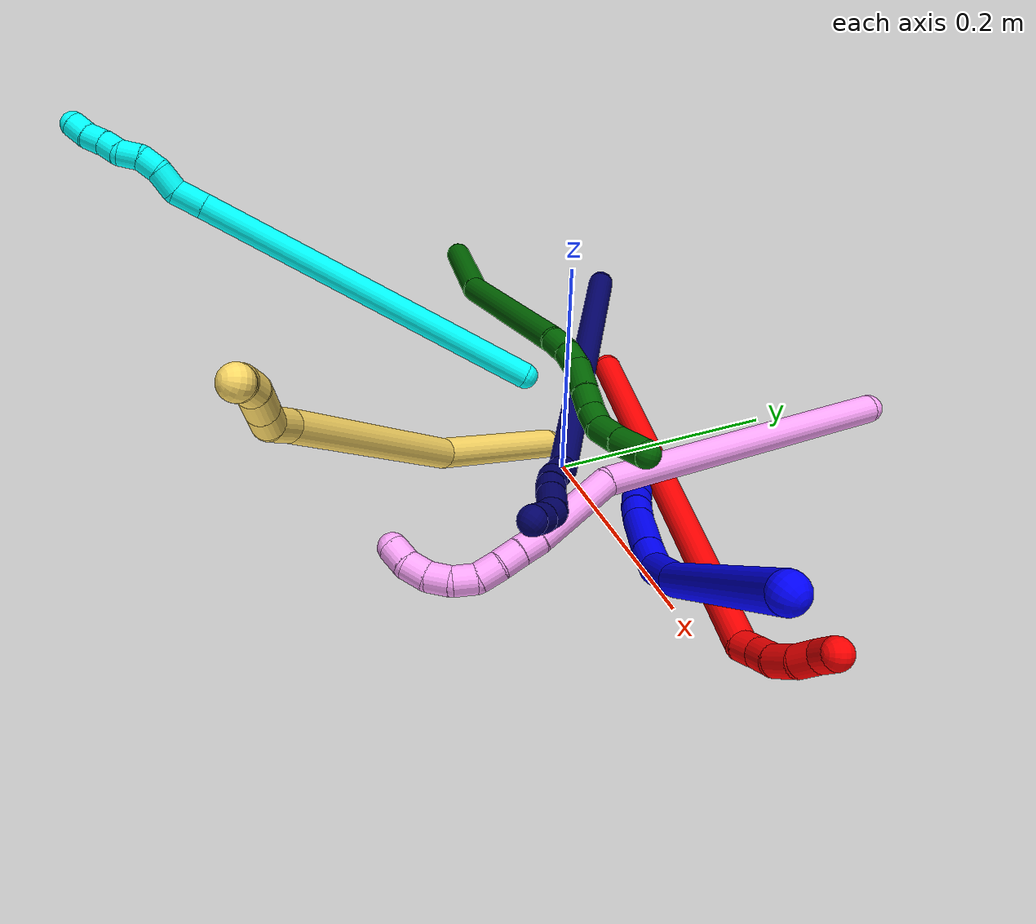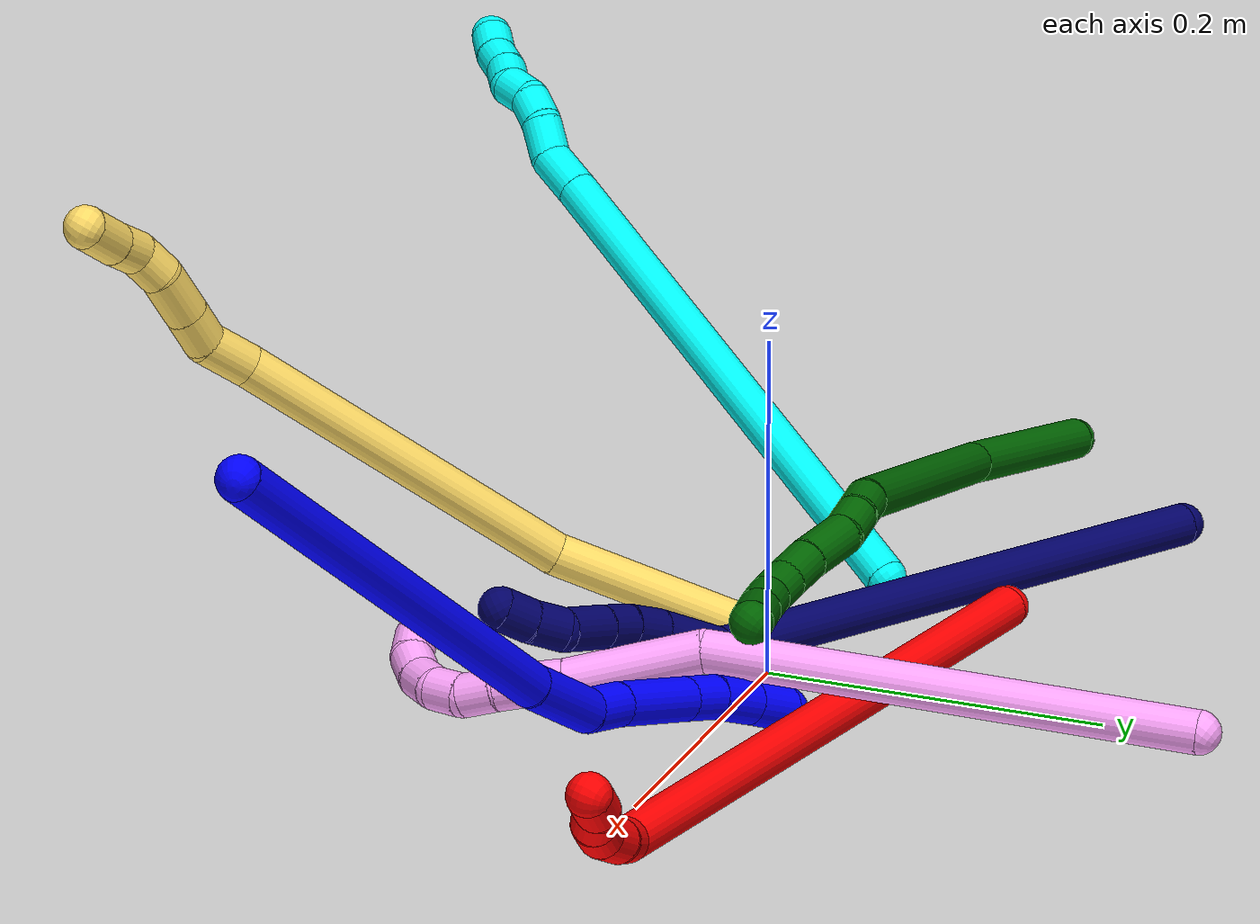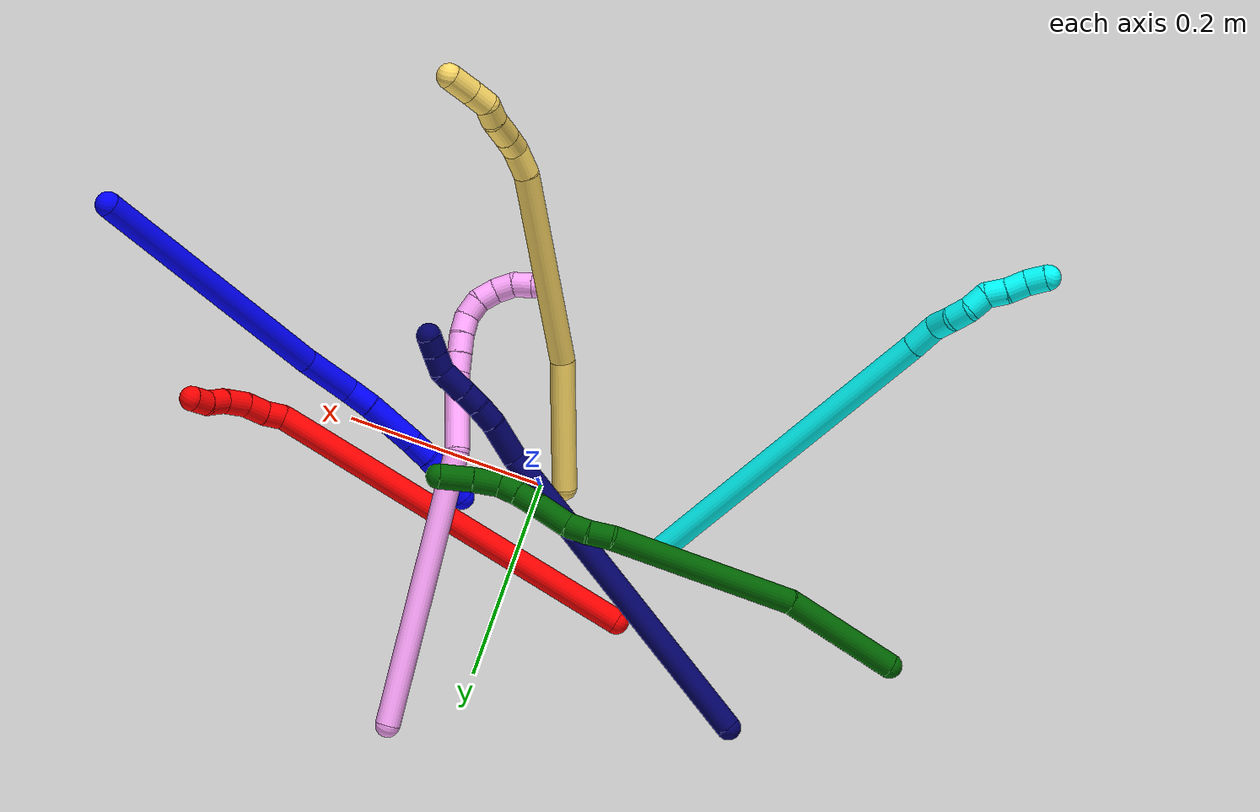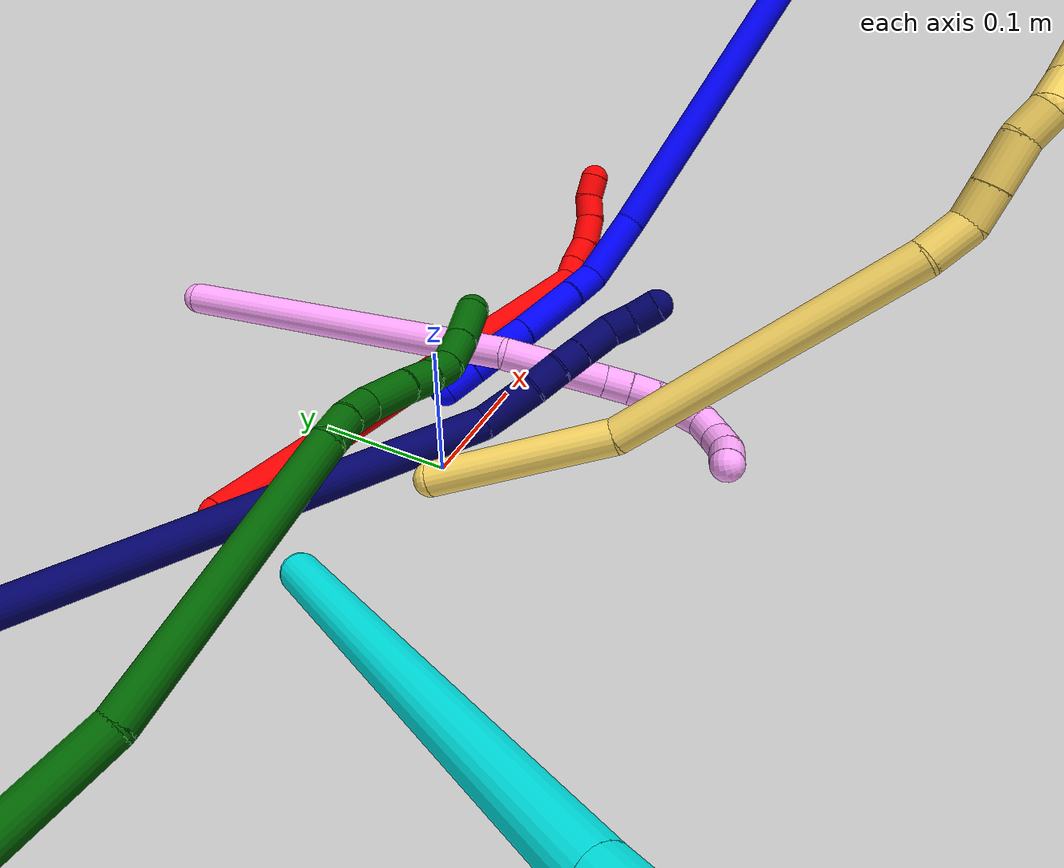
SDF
<sdf version="1.7">
 <world name="default">
  <plugin name="TubeGeneratorPlugin" filename="libtube_generator_plugin.so"/>
  <model name="photoneo_s_sensor">
   <static>1</static>
   <pose>0 0 2 1.57079 1.57079 3.14159</pose>
   <link name="link">
    <inertial><mass>0.1</mass></inertial>
    <sensor name="sensor" type="depth">
     <update_rate>30</update_rate>
     <camera>
      <horizontal_fov>1.22</horizontal_fov>
      <image><width>1920</width><height>1200</height><format>B8G8R8</format></image>
      <clip><near>0.1</near><far>4</far></clip>
      <depth_camera><output>points</output></depth_camera>
     </camera>
     <plugin name="camera_plugin" filename="libgazebo_ros_depth_camera.so">
      <baseline>0.2</baseline>
      <alwaysOn>1</alwaysOn>
      <updateRate>0.0</updateRate>
      <cameraName>camera_ir</cameraName>
      <imageTopicName>/camera/color/image_raw</imageTopicName>
      <cameraInfoTopicName>/camera/color/camera_info</cameraInfoTopicName>
      <depthImageTopicName>/camera/depth/image_raw</depthImageTopicName>
      <depthImageCameraInfoTopicName>/camera/depth/camera_info</depthImageCameraInfoTopicName>
      <pointCloudTopicName>/camera/depth/points</pointCloudTopicName>
      <frameName>fr_optical</frameName>
      <pointCloudCutoff>0.1</pointCloudCutoff>
      <pointCloudCutoffMax>2.0</pointCloudCutoffMax>
      <distortionK1>0</distortionK1>
      <distortionK2>0</distortionK2>
      <distortionK3>0</distortionK3>
      <distortionT1>0</distortionT1>
      <distortionT2>0</distortionT2>
      <CxPrime>0</CxPrime>
      <Cx>0</Cx>
      <Cy>0</Cy>
      <focalLength>0</focalLength>
      <hackBaseline>0</hackBaseline>
     </plugin>
    </sensor>
   </link>
  </model>
  <gravity>0 0 -9.8</gravity>
  <magnetic_field>6e-06 2.3e-05 -4.2e-05</magnetic_field>
  <atmosphere type="adiabatic"/>
  <physics name="default_physics" default="0" type="ode">
   <max_step_size>0.003</max_step_size>
   <real_time_factor>1</real_time_factor>
   <real_time_update_rate>1000</real_time_update_rate>
   <max_contacts>10000</max_contacts>
   <ode>
    <solver>
     <type>quick</type>
     <iters>100</iters>
     <sor>1.3</sor>
     <use_dynamic_moi_rescaling>0</use_dynamic_moi_rescaling>
    </solver>
    <constraints>
     <contact_max_correcting_vel>0</contact_max_correcting_vel>
     <contact_surface_layer>0.001</contact_surface_layer>
     <cfm>0</cfm>
     <erp>0.2</erp>
    </constraints>
   </ode>
  </physics>
  <scene><ambient>0.4 0.4 0.4 1</ambient><background>0.7 0.7 0.7 1</background><shadows>0</shadows></scene>
  <audio><device>default</device></audio>
  <spherical_coordinates>
   <surface_model>EARTH_WGS84</surface_model>
   <latitude_deg>0</latitude_deg>
   <longitude_deg>0</longitude_deg>
   <elevation>0</elevation>
   <heading_deg>0</heading_deg>
  </spherical_coordinates>
  <model name="bin">
   <static>1</static>
   <link name="bottom">
    <collision name="collision-bottom">
     <pose>0 0 -0.01 0 -0 0</pose>
     <geometry><box><size>0.8 0.6 0.02</size></box></geometry>
     <surface>
      <friction><ode><mu>100</mu><mu2>100</mu2></ode></friction>
      <contact><collide_bitmask>65535</collide_bitmask></contact>
     </surface>
    </collision>
   </link>
   <link name="west_wall">
    <collision name="collision-west_wall">
     <pose>-0.41 0 0.1 0 -0 0</pose>
     <geometry><box><size>0.02 0.6 0.2</size></box></geometry>
     <surface>
      <friction><ode><mu>100</mu><mu2>100</mu2></ode></friction>
      <contact><collide_bitmask>65535</collide_bitmask></contact>
     </surface>
    </collision>
   </link>
   <link name="east_wall">
    <collision name="collision-east_wall">
     <pose>0.41 0 0.1 0 -0 0</pose>
     <geometry><box><size>0.02 0.6 0.2</size></box></geometry>
     <surface>
      <friction><ode><mu>100</mu><mu2>100</mu2></ode></friction>
      <contact><collide_bitmask>65535</collide_bitmask></contact>
     </surface>
    </collision>
   </link>
   <link name="south_wall">
    <collision name="collision-south_wall">
     <pose>0 -0.31 0.1 0 -0 0</pose>
     <geometry><box><size>0.8 0.02 0.2</size></box></geometry>
     <surface>
      <friction><ode><mu>100</mu><mu2>100</mu2></ode></friction>
      <contact><collide_bitmask>65535</collide_bitmask></contact>
     </surface>
    </collision>
   </link>
   <link name="north_wall">
    <collision name="collision-north_wall">
     <pose>0 0.31 0.1 0 -0 0</pose>
     <geometry><box><size>0.8 0.02 0.2</size></box></geometry>
     <surface>
      <friction><ode><mu>100</mu><mu2>100</mu2></ode></friction>
      <contact><collide_bitmask>65535</collide_bitmask></contact>
     </surface>
    </collision>
   </link>
  </model>
  <model name="1">
   <static>0</static>
   <link name="1">
    <collision name="collision-cylinder-e_1_1_4">
     <pose>-0.011699 0.100759 -0.098282 -2.34375 -0.082925 0.196208</pose>
     <geometry><cylinder><radius>0.0125</radius><length>0.282479</length></cylinder></geometry>
     <surface>
      <friction><ode><mu>1.16</mu><mu2>1.16</mu2><slip1>0</slip1><slip2>0</slip2></ode></friction>
      <contact><ode><kp>1e+06</kp><kd>1</kd><max_vel>0</max_vel><min_depth>0.001</min_depth></ode></contact>
     </surface>
    </collision>
    <visual name="visual-cylinder-e_1_1_4">
     <pose>-0.011699 0.100759 -0.098282 -2.34375 -0.082925 0.196208</pose>
     <geometry><cylinder><radius>0.0125</radius><length>0.282479</length></cylinder></geometry>
     <material><ambient>0 0 1 1</ambient></material>
    </visual>
    <collision name="collision-cylinder-e_2_4_5">
     <pose>-0.02692 0.219373 -0.2191 -2.4716 -0.121907 0.347097</pose>
     <geometry><cylinder><radius>0.0125</radius><length>0.057934</length></cylinder></geometry>
     <surface>
      <friction><ode><mu>1.16</mu><mu2>1.16</mu2><slip1>0</slip1><slip2>0</slip2></ode></friction>
      <contact><ode><kp>1e+06</kp><kd>1</kd><max_vel>0</max_vel><min_depth>0.001</min_depth></ode></contact>
     </surface>
    </collision>
    <visual name="visual-cylinder-e_2_4_5">
     <pose>-0.02692 0.219373 -0.2191 -2.4716 -0.121907 0.347097</pose>
     <geometry><cylinder><radius>0.0125</radius><length>0.057934</length></cylinder></geometry>
     <material><ambient>0 0 1 1</ambient></material>
    </visual>
    <collision name="collision-cylinder-e_3_5_6">
     <pose>-0.035116 0.241589 -0.253339 -2.78481 -0.358048 1.57442</pose>
     <geometry><cylinder><radius>0.0125</radius><length>0.026667</length></cylinder></geometry>
     <surface>
      <friction><ode><mu>1.16</mu><mu2>1.16</mu2><slip1>0</slip1><slip2>0</slip2></ode></friction>
      <contact><ode><kp>1e+06</kp><kd>1</kd><max_vel>0</max_vel><min_depth>0.001</min_depth></ode></contact>
     </surface>
    </collision>
    <visual name="visual-cylinder-e_3_5_6">
     <pose>-0.035116 0.241589 -0.253339 -2.78481 -0.358048 1.57442</pose>
     <geometry><cylinder><radius>0.0125</radius><length>0.026667</length></cylinder></geometry>
     <material><ambient>0 0 1 1</ambient></material>
    </visual>
    <collision name="collision-cylinder-e_4_6_7">
     <pose>-0.050143 0.257111 -0.287795 -2.68562 -0.38786 1.40488</pose>
     <geometry><cylinder><radius>0.0125</radius><length>0.054756</length></cylinder></geometry>
     <surface>
      <friction><ode><mu>1.16</mu><mu2>1.16</mu2><slip1>0</slip1><slip2>0</slip2></ode></friction>
      <contact><ode><kp>1e+06</kp><kd>1</kd><max_vel>0</max_vel><min_depth>0.001</min_depth></ode></contact>
     </surface>
    </collision>
    <visual name="visual-cylinder-e_4_6_7">
     <pose>-0.050143 0.257111 -0.287795 -2.68562 -0.38786 1.40488</pose>
     <geometry><cylinder><radius>0.0125</radius><length>0.054756</length></cylinder></geometry>
     <material><ambient>0 0 1 1</ambient></material>
    </visual>
    <collision name="collision-cylinder-e_5_7_8">
     <pose>-0.0655 0.27322 -0.320007 -2.65948 -0.438281 1.4722</pose>
     <geometry><cylinder><radius>0.0125</radius><length>0.023575</length></cylinder></geometry>
     <surface>
      <friction><ode><mu>1.16</mu><mu2>1.16</mu2><slip1>0</slip1><slip2>0</slip2></ode></friction>
      <contact><ode><kp>1e+06</kp><kd>1</kd><max_vel>0</max_vel><min_depth>0.001</min_depth></ode></contact>
     </surface>
    </collision>
    <visual name="visual-cylinder-e_5_7_8">
     <pose>-0.0655 0.27322 -0.320007 -2.65948 -0.438281 1.4722</pose>
     <geometry><cylinder><radius>0.0125</radius><length>0.023575</length></cylinder></geometry>
     <material><ambient>0 0 1 1</ambient></material>
    </visual>
    <collision name="collision-cylinder-e_6_8_9">
     <pose>-0.076128 0.285972 -0.339487 -2.48003 -0.416917 1.10419</pose>
     <geometry><cylinder><radius>0.0125</radius><length>0.027784</length></cylinder></geometry>
     <surface>
      <friction><ode><mu>1.16</mu><mu2>1.16</mu2><slip1>0</slip1><slip2>0</slip2></ode></friction>
      <contact><ode><kp>1e+06</kp><kd>1</kd><max_vel>0</max_vel><min_depth>0.001</min_depth></ode></contact>
     </surface>
    </collision>
    <visual name="visual-cylinder-e_6_8_9">
     <pose>-0.076128 0.285972 -0.339487 -2.48003 -0.416917 1.10419</pose>
     <geometry><cylinder><radius>0.0125</radius><length>0.027784</length></cylinder></geometry>
     <material><ambient>0 0 1 1</ambient></material>
    </visual>
    <collision name="collision-cylinder-e_7_9_2">
     <pose>-0.087324 0.301517 -0.358925 -2.45352 -0.428678 1.09194</pose>
     <geometry><cylinder><radius>0.0125</radius><length>0.026804</length></cylinder></geometry>
     <surface>
      <friction><ode><mu>1.16</mu><mu2>1.16</mu2><slip1>0</slip1><slip2>0</slip2></ode></friction>
      <contact><ode><kp>1e+06</kp><kd>1</kd><max_vel>0</max_vel><min_depth>0.001</min_depth></ode></contact>
     </surface>
    </collision>
    <visual name="visual-cylinder-e_7_9_2">
     <pose>-0.087324 0.301517 -0.358925 -2.45352 -0.428678 1.09194</pose>
     <geometry><cylinder><radius>0.0125</radius><length>0.026804</length></cylinder></geometry>
     <material><ambient>0 0 1 1</ambient></material>
    </visual>
    <collision name="collision-sphere-2">
     <pose>-0.092895 0.309257 -0.368341 0 -0 0</pose>
     <geometry><sphere><radius>0.0125</radius></sphere></geometry>
     <surface>
      <friction><ode><mu>1.16</mu><mu2>1.16</mu2><slip1>0</slip1><slip2>0</slip2></ode></friction>
      <contact><ode><kp>1e+06</kp><kd>1</kd><max_vel>0</max_vel><min_depth>0.001</min_depth></ode></contact>
     </surface>
    </collision>
    <visual name="visual-sphere-2">
     <pose>-0.092895 0.309257 -0.368341 0 -0 0</pose>
     <geometry><sphere><radius>0.0125</radius></sphere></geometry>
     <material><ambient>0 0 1 1</ambient></material>
    </visual>
    <collision name="collision-sphere-9">
     <pose>-0.081753 0.293776 -0.349509 0 -0 0</pose>
     <geometry><sphere><radius>0.0125</radius></sphere></geometry>
     <surface>
      <friction><ode><mu>1.16</mu><mu2>1.16</mu2><slip1>0</slip1><slip2>0</slip2></ode></friction>
      <contact><ode><kp>1e+06</kp><kd>1</kd><max_vel>0</max_vel><min_depth>0.001</min_depth></ode></contact>
     </surface>
    </collision>
    <visual name="visual-sphere-9">
     <pose>-0.081753 0.293776 -0.349509 0 -0 0</pose>
     <geometry><sphere><radius>0.0125</radius></sphere></geometry>
     <material><ambient>0 0 1 1</ambient></material>
    </visual>
    <collision name="collision-sphere-4">
     <pose>-0.023398 0.201519 -0.196564 0 -0 0</pose>
     <geometry><sphere><radius>0.0125</radius></sphere></geometry>
     <surface>
      <friction><ode><mu>1.16</mu><mu2>1.16</mu2><slip1>0</slip1><slip2>0</slip2></ode></friction>
      <contact><ode><kp>1e+06</kp><kd>1</kd><max_vel>0</max_vel><min_depth>0.001</min_depth></ode></contact>
     </surface>
    </collision>
    <visual name="visual-sphere-4">
     <pose>-0.023398 0.201519 -0.196564 0 -0 0</pose>
     <geometry><sphere><radius>0.0125</radius></sphere></geometry>
     <material><ambient>0 0 1 1</ambient></material>
    </visual>
    <collision name="collision-sphere-1">
     <geometry><sphere><radius>0.0125</radius></sphere></geometry>
     <surface>
      <friction><ode><mu>1.16</mu><mu2>1.16</mu2><slip1>0</slip1><slip2>0</slip2></ode></friction>
      <contact><ode><kp>1e+06</kp><kd>1</kd><max_vel>0</max_vel><min_depth>0.001</min_depth></ode></contact>
     </surface>
    </collision>
    <visual name="visual-sphere-1">
     <geometry><sphere><radius>0.0125</radius></sphere></geometry>
     <material><ambient>0 0 1 1</ambient></material>
    </visual>
    <collision name="collision-sphere-8">
     <pose>-0.070502 0.278169 -0.329464 0 -0 0</pose>
     <geometry><sphere><radius>0.0125</radius></sphere></geometry>
     <surface>
      <friction><ode><mu>1.16</mu><mu2>1.16</mu2><slip1>0</slip1><slip2>0</slip2></ode></friction>
      <contact><ode><kp>1e+06</kp><kd>1</kd><max_vel>0</max_vel><min_depth>0.001</min_depth></ode></contact>
     </surface>
    </collision>
    <visual name="visual-sphere-8">
     <pose>-0.070502 0.278169 -0.329464 0 -0 0</pose>
     <geometry><sphere><radius>0.0125</radius></sphere></geometry>
     <material><ambient>0 0 1 1</ambient></material>
    </visual>
    <collision name="collision-sphere-5">
     <pose>-0.030443 0.237228 -0.241637 0 -0 0</pose>
     <geometry><sphere><radius>0.0125</radius></sphere></geometry>
     <surface>
      <friction><ode><mu>1.16</mu><mu2>1.16</mu2><slip1>0</slip1><slip2>0</slip2></ode></friction>
      <contact><ode><kp>1e+06</kp><kd>1</kd><max_vel>0</max_vel><min_depth>0.001</min_depth></ode></contact>
     </surface>
    </collision>
    <visual name="visual-sphere-5">
     <pose>-0.030443 0.237228 -0.241637 0 -0 0</pose>
     <geometry><sphere><radius>0.0125</radius></sphere></geometry>
     <material><ambient>0 0 1 1</ambient></material>
    </visual>
    <collision name="collision-sphere-6">
     <pose>-0.039788 0.245951 -0.26504 0 -0 0</pose>
     <geometry><sphere><radius>0.0125</radius></sphere></geometry>
     <surface>
      <friction><ode><mu>1.16</mu><mu2>1.16</mu2><slip1>0</slip1><slip2>0</slip2></ode></friction>
      <contact><ode><kp>1e+06</kp><kd>1</kd><max_vel>0</max_vel><min_depth>0.001</min_depth></ode></contact>
     </surface>
    </collision>
    <visual name="visual-sphere-6">
     <pose>-0.039788 0.245951 -0.26504 0 -0 0</pose>
     <geometry><sphere><radius>0.0125</radius></sphere></geometry>
     <material><ambient>0 0 1 1</ambient></material>
    </visual>
    <collision name="collision-sphere-7">
     <pose>-0.060498 0.268271 -0.310551 0 -0 0</pose>
     <geometry><sphere><radius>0.0125</radius></sphere></geometry>
     <surface>
      <friction><ode><mu>1.16</mu><mu2>1.16</mu2><slip1>0</slip1><slip2>0</slip2></ode></friction>
      <contact><ode><kp>1e+06</kp><kd>1</kd><max_vel>0</max_vel><min_depth>0.001</min_depth></ode></contact>
     </surface>
    </collision>
    <visual name="visual-sphere-7">
     <pose>-0.060498 0.268271 -0.310551 0 -0 0</pose>
     <geometry><sphere><radius>0.0125</radius></sphere></geometry>
     <material><ambient>0 0 1 1</ambient></material>
    </visual>
    <inertial>
     <pose>-0.029093 0.168322 -0.179135 0 -0 0</pose>
     <mass>0.5</mass>
     <inertia>
      <ixx>0.002258</ixx>
      <ixy>0</ixy>
      <ixz>0</ixz>
      <iyy>-0.000864</iyy>
      <iyz>0</iyz>
      <izz>-0.001231</izz>
     </inertia>
    </inertial>
   </link>
   <pose>0.460942 -0.104661 0.269229 -1.52079 0.434614 -1.35628</pose>
  </model>
  <model name="2">
   <static>0</static>
   <link name="2">
    <collision name="collision-cylinder-e_1_1_4">
     <pose>0.191513 -0.035185 0.012553 1.22811 1.37815 1.05228</pose>
     <geometry><cylinder><radius>0.0125</radius><length>0.390245</length></cylinder></geometry>
     <surface>
      <friction><ode><mu>1.16</mu><mu2>1.16</mu2><slip1>0</slip1><slip2>0</slip2></ode></friction>
      <contact><ode><kp>1e+06</kp><kd>1</kd><max_vel>0</max_vel><min_depth>0.001</min_depth></ode></contact>
     </surface>
    </collision>
    <visual name="visual-cylinder-e_1_1_4">
     <pose>0.191513 -0.035185 0.012553 1.22811 1.37815 1.05228</pose>
     <geometry><cylinder><radius>0.0125</radius><length>0.390245</length></cylinder></geometry>
     <material><ambient>1 0 0 1</ambient></material>
    </visual>
    <collision name="collision-cylinder-e_2_4_5">
     <pose>0.392519 -0.067656 0.023351 -2.14477 1.24267 -1.8416</pose>
     <geometry><cylinder><radius>0.0125</radius><length>0.020057</length></cylinder></geometry>
     <surface>
      <friction><ode><mu>1.16</mu><mu2>1.16</mu2><slip1>0</slip1><slip2>0</slip2></ode></friction>
      <contact><ode><kp>1e+06</kp><kd>1</kd><max_vel>0</max_vel><min_depth>0.001</min_depth></ode></contact>
     </surface>
    </collision>
    <visual name="visual-cylinder-e_2_4_5">
     <pose>0.392519 -0.067656 0.023351 -2.14477 1.24267 -1.8416</pose>
     <geometry><cylinder><radius>0.0125</radius><length>0.020057</length></cylinder></geometry>
     <material><ambient>1 0 0 1</ambient></material>
    </visual>
    <collision name="collision-cylinder-e_3_5_6">
     <pose>0.412744 -0.061145 0.022026 -1.45808 1.22869 -1.12446</pose>
     <geometry><cylinder><radius>0.0125</radius><length>0.022783</length></cylinder></geometry>
     <surface>
      <friction><ode><mu>1.16</mu><mu2>1.16</mu2><slip1>0</slip1><slip2>0</slip2></ode></friction>
      <contact><ode><kp>1e+06</kp><kd>1</kd><max_vel>0</max_vel><min_depth>0.001</min_depth></ode></contact>
     </surface>
    </collision>
    <visual name="visual-cylinder-e_3_5_6">
     <pose>0.412744 -0.061145 0.022026 -1.45808 1.22869 -1.12446</pose>
     <geometry><cylinder><radius>0.0125</radius><length>0.022783</length></cylinder></geometry>
     <material><ambient>1 0 0 1</ambient></material>
    </visual>
    <collision name="collision-cylinder-e_4_6_7">
     <pose>0.434331 -0.05053 0.020582 -1.83898 0.99353 -1.23638</pose>
     <geometry><cylinder><radius>0.0125</radius><length>0.025911</length></cylinder></geometry>
     <surface>
      <friction><ode><mu>1.16</mu><mu2>1.16</mu2><slip1>0</slip1><slip2>0</slip2></ode></friction>
      <contact><ode><kp>1e+06</kp><kd>1</kd><max_vel>0</max_vel><min_depth>0.001</min_depth></ode></contact>
     </surface>
    </collision>
    <visual name="visual-cylinder-e_4_6_7">
     <pose>0.434331 -0.05053 0.020582 -1.83898 0.99353 -1.23638</pose>
     <geometry><cylinder><radius>0.0125</radius><length>0.025911</length></cylinder></geometry>
     <material><ambient>1 0 0 1</ambient></material>
    </visual>
    <collision name="collision-cylinder-e_5_7_8">
     <pose>0.452387 -0.036876 0.015407 -2.02071 0.758856 -1.13208</pose>
     <geometry><cylinder><radius>0.0125</radius><length>0.020927</length></cylinder></geometry>
     <surface>
      <friction><ode><mu>1.16</mu><mu2>1.16</mu2><slip1>0</slip1><slip2>0</slip2></ode></friction>
      <contact><ode><kp>1e+06</kp><kd>1</kd><max_vel>0</max_vel><min_depth>0.001</min_depth></ode></contact>
     </surface>
    </collision>
    <visual name="visual-cylinder-e_5_7_8">
     <pose>0.452387 -0.036876 0.015407 -2.02071 0.758856 -1.13208</pose>
     <geometry><cylinder><radius>0.0125</radius><length>0.020927</length></cylinder></geometry>
     <material><ambient>1 0 0 1</ambient></material>
    </visual>
    <collision name="collision-cylinder-e_6_8_2">
     <pose>0.467515 -0.02388 0.012102 -1.57129 0.910298 -0.910691</pose>
     <geometry><cylinder><radius>0.0125</radius><length>0.020077</length></cylinder></geometry>
     <surface>
      <friction><ode><mu>1.16</mu><mu2>1.16</mu2><slip1>0</slip1><slip2>0</slip2></ode></friction>
      <contact><ode><kp>1e+06</kp><kd>1</kd><max_vel>0</max_vel><min_depth>0.001</min_depth></ode></contact>
     </surface>
    </collision>
    <visual name="visual-cylinder-e_6_8_2">
     <pose>0.467515 -0.02388 0.012102 -1.57129 0.910298 -0.910691</pose>
     <geometry><cylinder><radius>0.0125</radius><length>0.020077</length></cylinder></geometry>
     <material><ambient>1 0 0 1</ambient></material>
    </visual>
    <collision name="collision-sphere-2">
     <pose>0.475442 -0.017721 0.012099 0 -0 0</pose>
     <geometry><sphere><radius>0.0125</radius></sphere></geometry>
     <surface>
      <friction><ode><mu>1.16</mu><mu2>1.16</mu2><slip1>0</slip1><slip2>0</slip2></ode></friction>
      <contact><ode><kp>1e+06</kp><kd>1</kd><max_vel>0</max_vel><min_depth>0.001</min_depth></ode></contact>
     </surface>
    </collision>
    <visual name="visual-sphere-2">
     <pose>0.475442 -0.017721 0.012099 0 -0 0</pose>
     <geometry><sphere><radius>0.0125</radius></sphere></geometry>
     <material><ambient>1 0 0 1</ambient></material>
    </visual>
    <collision name="collision-sphere-4">
     <pose>0.383026 -0.07037 0.025106 0 -0 0</pose>
     <geometry><sphere><radius>0.0125</radius></sphere></geometry>
     <surface>
      <friction><ode><mu>1.16</mu><mu2>1.16</mu2><slip1>0</slip1><slip2>0</slip2></ode></friction>
      <contact><ode><kp>1e+06</kp><kd>1</kd><max_vel>0</max_vel><min_depth>0.001</min_depth></ode></contact>
     </surface>
    </collision>
    <visual name="visual-sphere-4">
     <pose>0.383026 -0.07037 0.025106 0 -0 0</pose>
     <geometry><sphere><radius>0.0125</radius></sphere></geometry>
     <material><ambient>1 0 0 1</ambient></material>
    </visual>
    <collision name="collision-sphere-1">
     <geometry><sphere><radius>0.0125</radius></sphere></geometry>
     <surface>
      <friction><ode><mu>1.16</mu><mu2>1.16</mu2><slip1>0</slip1><slip2>0</slip2></ode></friction>
      <contact><ode><kp>1e+06</kp><kd>1</kd><max_vel>0</max_vel><min_depth>0.001</min_depth></ode></contact>
     </surface>
    </collision>
    <visual name="visual-sphere-1">
     <geometry><sphere><radius>0.0125</radius></sphere></geometry>
     <material><ambient>1 0 0 1</ambient></material>
    </visual>
    <collision name="collision-sphere-8">
     <pose>0.459587 -0.030039 0.012105 0 -0 0</pose>
     <geometry><sphere><radius>0.0125</radius></sphere></geometry>
     <surface>
      <friction><ode><mu>1.16</mu><mu2>1.16</mu2><slip1>0</slip1><slip2>0</slip2></ode></friction>
      <contact><ode><kp>1e+06</kp><kd>1</kd><max_vel>0</max_vel><min_depth>0.001</min_depth></ode></contact>
     </surface>
    </collision>
    <visual name="visual-sphere-8">
     <pose>0.459587 -0.030039 0.012105 0 -0 0</pose>
     <geometry><sphere><radius>0.0125</radius></sphere></geometry>
     <material><ambient>1 0 0 1</ambient></material>
    </visual>
    <collision name="collision-sphere-5">
     <pose>0.402013 -0.064942 0.021596 0 -0 0</pose>
     <geometry><sphere><radius>0.0125</radius></sphere></geometry>
     <surface>
      <friction><ode><mu>1.16</mu><mu2>1.16</mu2><slip1>0</slip1><slip2>0</slip2></ode></friction>
      <contact><ode><kp>1e+06</kp><kd>1</kd><max_vel>0</max_vel><min_depth>0.001</min_depth></ode></contact>
     </surface>
    </collision>
    <visual name="visual-sphere-5">
     <pose>0.402013 -0.064942 0.021596 0 -0 0</pose>
     <geometry><sphere><radius>0.0125</radius></sphere></geometry>
     <material><ambient>1 0 0 1</ambient></material>
    </visual>
    <collision name="collision-sphere-6">
     <pose>0.423475 -0.057348 0.022456 0 -0 0</pose>
     <geometry><sphere><radius>0.0125</radius></sphere></geometry>
     <surface>
      <friction><ode><mu>1.16</mu><mu2>1.16</mu2><slip1>0</slip1><slip2>0</slip2></ode></friction>
      <contact><ode><kp>1e+06</kp><kd>1</kd><max_vel>0</max_vel><min_depth>0.001</min_depth></ode></contact>
     </surface>
    </collision>
    <visual name="visual-sphere-6">
     <pose>0.423475 -0.057348 0.022456 0 -0 0</pose>
     <geometry><sphere><radius>0.0125</radius></sphere></geometry>
     <material><ambient>1 0 0 1</ambient></material>
    </visual>
    <collision name="collision-sphere-7">
     <pose>0.445187 -0.043713 0.018709 0 -0 0</pose>
     <geometry><sphere><radius>0.0125</radius></sphere></geometry>
     <surface>
      <friction><ode><mu>1.16</mu><mu2>1.16</mu2><slip1>0</slip1><slip2>0</slip2></ode></friction>
      <contact><ode><kp>1e+06</kp><kd>1</kd><max_vel>0</max_vel><min_depth>0.001</min_depth></ode></contact>
     </surface>
    </collision>
    <visual name="visual-sphere-7">
     <pose>0.445187 -0.043713 0.018709 0 -0 0</pose>
     <geometry><sphere><radius>0.0125</radius></sphere></geometry>
     <material><ambient>1 0 0 1</ambient></material>
    </visual>
    <inertial>
     <pose>0.244241 -0.038083 0.013935 0 -0 0</pose>
     <mass>0.5</mass>
     <inertia>
      <ixx>0.001332</ixx>
      <ixy>0</ixy>
      <ixz>0</ixz>
      <iyy>0.005643</iyy>
      <iyz>0</iyz>
      <izz>-0.003991</izz>
     </inertia>
    </inertial>
   </link>
   <pose>-0.117367 0.102978 0.011497 1.36763 -0.165202 -0.110599</pose>
  </model>
  <model name="3">
   <static>0</static>
   <link name="3">
    <collision name="collision-cylinder-e_1_1_4">
     <pose>-0.026283 -0.049452 0.163172 0.294264 -0.152947 -0.022711</pose>
     <geometry><cylinder><radius>0.0125</radius><length>0.34503</length></cylinder></geometry>
     <surface>
      <friction><ode><mu>1.16</mu><mu2>1.16</mu2><slip1>0</slip1><slip2>0</slip2></ode></friction>
      <contact><ode><kp>1e+06</kp><kd>1</kd><max_vel>0</max_vel><min_depth>0.001</min_depth></ode></contact>
     </surface>
    </collision>
    <visual name="visual-cylinder-e_1_1_4">
     <pose>-0.026283 -0.049452 0.163172 0.294264 -0.152947 -0.022711</pose>
     <geometry><cylinder><radius>0.0125</radius><length>0.34503</length></cylinder></geometry>
     <material><ambient>0.003922 1 0.996078 1</ambient></material>
    </visual>
    <collision name="collision-cylinder-e_2_4_5">
     <pose>-0.054302 -0.102875 0.340395 0.275486 -0.118378 -0.016428</pose>
     <geometry><cylinder><radius>0.0125</radius><length>0.029407</length></cylinder></geometry>
     <surface>
      <friction><ode><mu>1.16</mu><mu2>1.16</mu2><slip1>0</slip1><slip2>0</slip2></ode></friction>
      <contact><ode><kp>1e+06</kp><kd>1</kd><max_vel>0</max_vel><min_depth>0.001</min_depth></ode></contact>
     </surface>
    </collision>
    <visual name="visual-cylinder-e_2_4_5">
     <pose>-0.054302 -0.102875 0.340395 0.275486 -0.118378 -0.016428</pose>
     <geometry><cylinder><radius>0.0125</radius><length>0.029407</length></cylinder></geometry>
     <material><ambient>0.003922 1 0.996078 1</ambient></material>
    </visual>
    <collision name="collision-cylinder-e_3_5_6">
     <pose>-0.060484 -0.105799 0.365669 -0.092973 -0.375601 0.017681</pose>
     <geometry><cylinder><radius>0.0125</radius><length>0.024236</length></cylinder></geometry>
     <surface>
      <friction><ode><mu>1.16</mu><mu2>1.16</mu2><slip1>0</slip1><slip2>0</slip2></ode></friction>
      <contact><ode><kp>1e+06</kp><kd>1</kd><max_vel>0</max_vel><min_depth>0.001</min_depth></ode></contact>
     </surface>
    </collision>
    <visual name="visual-cylinder-e_3_5_6">
     <pose>-0.060484 -0.105799 0.365669 -0.092973 -0.375601 0.017681</pose>
     <geometry><cylinder><radius>0.0125</radius><length>0.024236</length></cylinder></geometry>
     <material><ambient>0.003922 1 0.996078 1</ambient></material>
    </visual>
    <collision name="collision-cylinder-e_4_6_7">
     <pose>-0.068228 -0.107142 0.386208 0.251067 -0.330456 -0.04208</pose>
     <geometry><cylinder><radius>0.0125</radius><length>0.020332</length></cylinder></geometry>
     <surface>
      <friction><ode><mu>1.16</mu><mu2>1.16</mu2><slip1>0</slip1><slip2>0</slip2></ode></friction>
      <contact><ode><kp>1e+06</kp><kd>1</kd><max_vel>0</max_vel><min_depth>0.001</min_depth></ode></contact>
     </surface>
    </collision>
    <visual name="visual-cylinder-e_4_6_7">
     <pose>-0.068228 -0.107142 0.386208 0.251067 -0.330456 -0.04208</pose>
     <geometry><cylinder><radius>0.0125</radius><length>0.020332</length></cylinder></geometry>
     <material><ambient>0.003922 1 0.996078 1</ambient></material>
    </visual>
    <collision name="collision-cylinder-e_5_7_8">
     <pose>-0.072146 -0.115159 0.403977 0.587366 -0.060905 -0.018425</pose>
     <geometry><cylinder><radius>0.0125</radius><length>0.02035</length></cylinder></geometry>
     <surface>
      <friction><ode><mu>1.16</mu><mu2>1.16</mu2><slip1>0</slip1><slip2>0</slip2></ode></friction>
      <contact><ode><kp>1e+06</kp><kd>1</kd><max_vel>0</max_vel><min_depth>0.001</min_depth></ode></contact>
     </surface>
    </collision>
    <visual name="visual-cylinder-e_5_7_8">
     <pose>-0.072146 -0.115159 0.403977 0.587366 -0.060905 -0.018425</pose>
     <geometry><cylinder><radius>0.0125</radius><length>0.02035</length></cylinder></geometry>
     <material><ambient>0.003922 1 0.996078 1</ambient></material>
    </visual>
    <collision name="collision-cylinder-e_6_8_9">
     <pose>-0.078221 -0.125872 0.419177 0.645876 -0.57337 -0.196679</pose>
     <geometry><cylinder><radius>0.0125</radius><length>0.020113</length></cylinder></geometry>
     <surface>
      <friction><ode><mu>1.16</mu><mu2>1.16</mu2><slip1>0</slip1><slip2>0</slip2></ode></friction>
      <contact><ode><kp>1e+06</kp><kd>1</kd><max_vel>0</max_vel><min_depth>0.001</min_depth></ode></contact>
     </surface>
    </collision>
    <visual name="visual-cylinder-e_6_8_9">
     <pose>-0.078221 -0.125872 0.419177 0.645876 -0.57337 -0.196679</pose>
     <geometry><cylinder><radius>0.0125</radius><length>0.020113</length></cylinder></geometry>
     <material><ambient>0.003922 1 0.996078 1</ambient></material>
    </visual>
    <collision name="collision-cylinder-e_7_9_10">
     <pose>-0.087453 -0.136583 0.433591 0.633007 -0.378047 -0.125148</pose>
     <geometry><cylinder><radius>0.0125</radius><length>0.020466</length></cylinder></geometry>
     <surface>
      <friction><ode><mu>1.16</mu><mu2>1.16</mu2><slip1>0</slip1><slip2>0</slip2></ode></friction>
      <contact><ode><kp>1e+06</kp><kd>1</kd><max_vel>0</max_vel><min_depth>0.001</min_depth></ode></contact>
     </surface>
    </collision>
    <visual name="visual-cylinder-e_7_9_10">
     <pose>-0.087453 -0.136583 0.433591 0.633007 -0.378047 -0.125148</pose>
     <geometry><cylinder><radius>0.0125</radius><length>0.020466</length></cylinder></geometry>
     <material><ambient>0.003922 1 0.996078 1</ambient></material>
    </visual>
    <collision name="collision-cylinder-e_8_10_2">
     <pose>-0.096574 -0.146 0.448858 0.462738 -0.561714 -0.135717</pose>
     <geometry><cylinder><radius>0.0125</radius><length>0.020066</length></cylinder></geometry>
     <surface>
      <friction><ode><mu>1.16</mu><mu2>1.16</mu2><slip1>0</slip1><slip2>0</slip2></ode></friction>
      <contact><ode><kp>1e+06</kp><kd>1</kd><max_vel>0</max_vel><min_depth>0.001</min_depth></ode></contact>
     </surface>
    </collision>
    <visual name="visual-cylinder-e_8_10_2">
     <pose>-0.096574 -0.146 0.448858 0.462738 -0.561714 -0.135717</pose>
     <geometry><cylinder><radius>0.0125</radius><length>0.020066</length></cylinder></geometry>
     <material><ambient>0.003922 1 0.996078 1</ambient></material>
    </visual>
    <collision name="collision-sphere-2">
     <pose>-0.101918 -0.149791 0.456456 0 -0 0</pose>
     <geometry><sphere><radius>0.0125</radius></sphere></geometry>
     <surface>
      <friction><ode><mu>1.16</mu><mu2>1.16</mu2><slip1>0</slip1><slip2>0</slip2></ode></friction>
      <contact><ode><kp>1e+06</kp><kd>1</kd><max_vel>0</max_vel><min_depth>0.001</min_depth></ode></contact>
     </surface>
    </collision>
    <visual name="visual-sphere-2">
     <pose>-0.101918 -0.149791 0.456456 0 -0 0</pose>
     <geometry><sphere><radius>0.0125</radius></sphere></geometry>
     <material><ambient>0.003922 1 0.996078 1</ambient></material>
    </visual>
    <collision name="collision-sphere-10">
     <pose>-0.09123 -0.142209 0.441259 0 -0 0</pose>
     <geometry><sphere><radius>0.0125</radius></sphere></geometry>
     <surface>
      <friction><ode><mu>1.16</mu><mu2>1.16</mu2><slip1>0</slip1><slip2>0</slip2></ode></friction>
      <contact><ode><kp>1e+06</kp><kd>1</kd><max_vel>0</max_vel><min_depth>0.001</min_depth></ode></contact>
     </surface>
    </collision>
    <visual name="visual-sphere-10">
     <pose>-0.09123 -0.142209 0.441259 0 -0 0</pose>
     <geometry><sphere><radius>0.0125</radius></sphere></geometry>
     <material><ambient>0.003922 1 0.996078 1</ambient></material>
    </visual>
    <collision name="collision-sphere-9">
     <pose>-0.083676 -0.130957 0.425924 0 -0 0</pose>
     <geometry><sphere><radius>0.0125</radius></sphere></geometry>
     <surface>
      <friction><ode><mu>1.16</mu><mu2>1.16</mu2><slip1>0</slip1><slip2>0</slip2></ode></friction>
      <contact><ode><kp>1e+06</kp><kd>1</kd><max_vel>0</max_vel><min_depth>0.001</min_depth></ode></contact>
     </surface>
    </collision>
    <visual name="visual-sphere-9">
     <pose>-0.083676 -0.130957 0.425924 0 -0 0</pose>
     <geometry><sphere><radius>0.0125</radius></sphere></geometry>
     <material><ambient>0.003922 1 0.996078 1</ambient></material>
    </visual>
    <collision name="collision-sphere-4">
     <pose>-0.052566 -0.098903 0.326345 0 -0 0</pose>
     <geometry><sphere><radius>0.0125</radius></sphere></geometry>
     <surface>
      <friction><ode><mu>1.16</mu><mu2>1.16</mu2><slip1>0</slip1><slip2>0</slip2></ode></friction>
      <contact><ode><kp>1e+06</kp><kd>1</kd><max_vel>0</max_vel><min_depth>0.001</min_depth></ode></contact>
     </surface>
    </collision>
    <visual name="visual-sphere-4">
     <pose>-0.052566 -0.098903 0.326345 0 -0 0</pose>
     <geometry><sphere><radius>0.0125</radius></sphere></geometry>
     <material><ambient>0.003922 1 0.996078 1</ambient></material>
    </visual>
    <collision name="collision-sphere-1">
     <geometry><sphere><radius>0.0125</radius></sphere></geometry>
     <surface>
      <friction><ode><mu>1.16</mu><mu2>1.16</mu2><slip1>0</slip1><slip2>0</slip2></ode></friction>
      <contact><ode><kp>1e+06</kp><kd>1</kd><max_vel>0</max_vel><min_depth>0.001</min_depth></ode></contact>
     </surface>
    </collision>
    <visual name="visual-sphere-1">
     <geometry><sphere><radius>0.0125</radius></sphere></geometry>
     <material><ambient>0.003922 1 0.996078 1</ambient></material>
    </visual>
    <collision name="collision-sphere-8">
     <pose>-0.072765 -0.120787 0.412431 0 -0 0</pose>
     <geometry><sphere><radius>0.0125</radius></sphere></geometry>
     <surface>
      <friction><ode><mu>1.16</mu><mu2>1.16</mu2><slip1>0</slip1><slip2>0</slip2></ode></friction>
      <contact><ode><kp>1e+06</kp><kd>1</kd><max_vel>0</max_vel><min_depth>0.001</min_depth></ode></contact>
     </surface>
    </collision>
    <visual name="visual-sphere-8">
     <pose>-0.072765 -0.120787 0.412431 0 -0 0</pose>
     <geometry><sphere><radius>0.0125</radius></sphere></geometry>
     <material><ambient>0.003922 1 0.996078 1</ambient></material>
    </visual>
    <collision name="collision-sphere-5">
     <pose>-0.056039 -0.106846 0.354444 0 -0 0</pose>
     <geometry><sphere><radius>0.0125</radius></sphere></geometry>
     <surface>
      <friction><ode><mu>1.16</mu><mu2>1.16</mu2><slip1>0</slip1><slip2>0</slip2></ode></friction>
      <contact><ode><kp>1e+06</kp><kd>1</kd><max_vel>0</max_vel><min_depth>0.001</min_depth></ode></contact>
     </surface>
    </collision>
    <visual name="visual-sphere-5">
     <pose>-0.056039 -0.106846 0.354444 0 -0 0</pose>
     <geometry><sphere><radius>0.0125</radius></sphere></geometry>
     <material><ambient>0.003922 1 0.996078 1</ambient></material>
    </visual>
    <collision name="collision-sphere-6">
     <pose>-0.06493 -0.104753 0.376894 0 -0 0</pose>
     <geometry><sphere><radius>0.0125</radius></sphere></geometry>
     <surface>
      <friction><ode><mu>1.16</mu><mu2>1.16</mu2><slip1>0</slip1><slip2>0</slip2></ode></friction>
      <contact><ode><kp>1e+06</kp><kd>1</kd><max_vel>0</max_vel><min_depth>0.001</min_depth></ode></contact>
     </surface>
    </collision>
    <visual name="visual-sphere-6">
     <pose>-0.06493 -0.104753 0.376894 0 -0 0</pose>
     <geometry><sphere><radius>0.0125</radius></sphere></geometry>
     <material><ambient>0.003922 1 0.996078 1</ambient></material>
    </visual>
    <collision name="collision-sphere-7">
     <pose>-0.071527 -0.109531 0.395523 0 -0 0</pose>
     <geometry><sphere><radius>0.0125</radius></sphere></geometry>
     <surface>
      <friction><ode><mu>1.16</mu><mu2>1.16</mu2><slip1>0</slip1><slip2>0</slip2></ode></friction>
      <contact><ode><kp>1e+06</kp><kd>1</kd><max_vel>0</max_vel><min_depth>0.001</min_depth></ode></contact>
     </surface>
    </collision>
    <visual name="visual-sphere-7">
     <pose>-0.071527 -0.109531 0.395523 0 -0 0</pose>
     <geometry><sphere><radius>0.0125</radius></sphere></geometry>
     <material><ambient>0.003922 1 0.996078 1</ambient></material>
    </visual>
    <inertial>
     <pose>-0.040575 -0.07086 0.235113 0 -0 0</pose>
     <mass>0.5</mass>
     <inertia>
      <ixx>0.003322</ixx>
      <ixy>0</ixy>
      <ixz>0</ixz>
      <iyy>0.003214</iyy>
      <iyz>0</iyz>
      <izz>0.001552</izz>
     </inertia>
    </inertial>
   </link>
   <pose>-0.134037 0.022074 0.011498 0.829934 0.236347 -0.498294</pose>
  </model>
  <model name="4">
   <static>0</static>
   <link name="4">
    <collision name="collision-cylinder-e_1_1_4">
     <pose>0.012541 -0.062203 0.124909 0.462038 0.089632 0.021096</pose>
     <geometry><cylinder><radius>0.0125</radius><length>0.280205</length></cylinder></geometry>
     <surface>
      <friction><ode><mu>1.16</mu><mu2>1.16</mu2><slip1>0</slip1><slip2>0</slip2></ode></friction>
      <contact><ode><kp>1e+06</kp><kd>1</kd><max_vel>0</max_vel><min_depth>0.001</min_depth></ode></contact>
     </surface>
    </collision>
    <visual name="visual-cylinder-e_1_1_4">
     <pose>0.012541 -0.062203 0.124909 0.462038 0.089632 0.021096</pose>
     <geometry><cylinder><radius>0.0125</radius><length>0.280205</length></cylinder></geometry>
     <material><ambient>1 0.65098 0.996078 1</ambient></material>
    </visual>
    <collision name="collision-cylinder-e_2_4_5">
     <pose>0.03692 -0.15123 0.276367 0.790534 0.303961 0.127632</pose>
     <geometry><cylinder><radius>0.0125</radius><length>0.079107</length></cylinder></geometry>
     <surface>
      <friction><ode><mu>1.16</mu><mu2>1.16</mu2><slip1>0</slip1><slip2>0</slip2></ode></friction>
      <contact><ode><kp>1e+06</kp><kd>1</kd><max_vel>0</max_vel><min_depth>0.001</min_depth></ode></contact>
     </surface>
    </collision>
    <visual name="visual-cylinder-e_2_4_5">
     <pose>0.03692 -0.15123 0.276367 0.790534 0.303961 0.127632</pose>
     <geometry><cylinder><radius>0.0125</radius><length>0.079107</length></cylinder></geometry>
     <material><ambient>1 0.65098 0.996078 1</ambient></material>
    </visual>
    <collision name="collision-cylinder-e_3_5_6">
     <pose>0.050852 -0.184408 0.310428 0.702109 0.20966 0.077027</pose>
     <geometry><cylinder><radius>0.0125</radius><length>0.020121</length></cylinder></geometry>
     <surface>
      <friction><ode><mu>1.16</mu><mu2>1.16</mu2><slip1>0</slip1><slip2>0</slip2></ode></friction>
      <contact><ode><kp>1e+06</kp><kd>1</kd><max_vel>0</max_vel><min_depth>0.001</min_depth></ode></contact>
     </surface>
    </collision>
    <visual name="visual-cylinder-e_3_5_6">
     <pose>0.050852 -0.184408 0.310428 0.702109 0.20966 0.077027</pose>
     <geometry><cylinder><radius>0.0125</radius><length>0.020121</length></cylinder></geometry>
     <material><ambient>1 0.65098 0.996078 1</ambient></material>
    </visual>
    <collision name="collision-cylinder-e_4_6_7">
     <pose>0.054954 -0.197472 0.32512 0.751593 0.201511 0.079733</pose>
     <geometry><cylinder><radius>0.0125</radius><length>0.020059</length></cylinder></geometry>
     <surface>
      <friction><ode><mu>1.16</mu><mu2>1.16</mu2><slip1>0</slip1><slip2>0</slip2></ode></friction>
      <contact><ode><kp>1e+06</kp><kd>1</kd><max_vel>0</max_vel><min_depth>0.001</min_depth></ode></contact>
     </surface>
    </collision>
    <visual name="visual-cylinder-e_4_6_7">
     <pose>0.054954 -0.197472 0.32512 0.751593 0.201511 0.079733</pose>
     <geometry><cylinder><radius>0.0125</radius><length>0.020059</length></cylinder></geometry>
     <material><ambient>1 0.65098 0.996078 1</ambient></material>
    </visual>
    <collision name="collision-cylinder-e_5_7_8">
     <pose>0.057458 -0.211636 0.339267 0.819096 0.048671 0.021131</pose>
     <geometry><cylinder><radius>0.0125</radius><length>0.020431</length></cylinder></geometry>
     <surface>
      <friction><ode><mu>1.16</mu><mu2>1.16</mu2><slip1>0</slip1><slip2>0</slip2></ode></friction>
      <contact><ode><kp>1e+06</kp><kd>1</kd><max_vel>0</max_vel><min_depth>0.001</min_depth></ode></contact>
     </surface>
    </collision>
    <visual name="visual-cylinder-e_5_7_8">
     <pose>0.057458 -0.211636 0.339267 0.819096 0.048671 0.021131</pose>
     <geometry><cylinder><radius>0.0125</radius><length>0.020431</length></cylinder></geometry>
     <material><ambient>1 0.65098 0.996078 1</ambient></material>
    </visual>
    <collision name="collision-cylinder-e_6_8_9">
     <pose>0.05512 -0.223874 0.354569 0.521094 -0.286839 -0.076964</pose>
     <geometry><cylinder><radius>0.0125</radius><length>0.020037</length></cylinder></geometry>
     <surface>
      <friction><ode><mu>1.16</mu><mu2>1.16</mu2><slip1>0</slip1><slip2>0</slip2></ode></friction>
      <contact><ode><kp>1e+06</kp><kd>1</kd><max_vel>0</max_vel><min_depth>0.001</min_depth></ode></contact>
     </surface>
    </collision>
    <visual name="visual-cylinder-e_6_8_9">
     <pose>0.05512 -0.223874 0.354569 0.521094 -0.286839 -0.076964</pose>
     <geometry><cylinder><radius>0.0125</radius><length>0.020037</length></cylinder></geometry>
     <material><ambient>1 0.65098 0.996078 1</ambient></material>
    </visual>
    <collision name="collision-cylinder-e_7_9_10">
     <pose>0.045743 -0.232091 0.36967 0.469473 -0.711576 -0.177268</pose>
     <geometry><cylinder><radius>0.0125</radius><length>0.020039</length></cylinder></geometry>
     <surface>
      <friction><ode><mu>1.16</mu><mu2>1.16</mu2><slip1>0</slip1><slip2>0</slip2></ode></friction>
      <contact><ode><kp>1e+06</kp><kd>1</kd><max_vel>0</max_vel><min_depth>0.001</min_depth></ode></contact>
     </surface>
    </collision>
    <visual name="visual-cylinder-e_7_9_10">
     <pose>0.045743 -0.232091 0.36967 0.469473 -0.711576 -0.177268</pose>
     <geometry><cylinder><radius>0.0125</radius><length>0.020039</length></cylinder></geometry>
     <material><ambient>1 0.65098 0.996078 1</ambient></material>
    </visual>
    <collision name="collision-cylinder-e_8_10_11">
     <pose>0.03161 -0.235962 0.382933 0.067369 -0.861811 -0.03098</pose>
     <geometry><cylinder><radius>0.0125</radius><length>0.02</length></cylinder></geometry>
     <surface>
      <friction><ode><mu>1.16</mu><mu2>1.16</mu2><slip1>0</slip1><slip2>0</slip2></ode></friction>
      <contact><ode><kp>1e+06</kp><kd>1</kd><max_vel>0</max_vel><min_depth>0.001</min_depth></ode></contact>
     </surface>
    </collision>
    <visual name="visual-cylinder-e_8_10_11">
     <pose>0.03161 -0.235962 0.382933 0.067369 -0.861811 -0.03098</pose>
     <geometry><cylinder><radius>0.0125</radius><length>0.02</length></cylinder></geometry>
     <material><ambient>1 0.65098 0.996078 1</ambient></material>
    </visual>
    <collision name="collision-cylinder-e_9_11_2">
     <pose>0.01489 -0.234937 0.39324 -0.366515 -1.15036 0.239162</pose>
     <geometry><cylinder><radius>0.0125</radius><length>0.020001</length></cylinder></geometry>
     <surface>
      <friction><ode><mu>1.16</mu><mu2>1.16</mu2><slip1>0</slip1><slip2>0</slip2></ode></friction>
      <contact><ode><kp>1e+06</kp><kd>1</kd><max_vel>0</max_vel><min_depth>0.001</min_depth></ode></contact>
     </surface>
    </collision>
    <visual name="visual-cylinder-e_9_11_2">
     <pose>0.01489 -0.234937 0.39324 -0.366515 -1.15036 0.239162</pose>
     <geometry><cylinder><radius>0.0125</radius><length>0.020001</length></cylinder></geometry>
     <material><ambient>1 0.65098 0.996078 1</ambient></material>
    </visual>
    <collision name="collision-sphere-2">
     <pose>0.005761 -0.233475 0.39705 0 -0 0</pose>
     <geometry><sphere><radius>0.0125</radius></sphere></geometry>
     <surface>
      <friction><ode><mu>1.16</mu><mu2>1.16</mu2><slip1>0</slip1><slip2>0</slip2></ode></friction>
      <contact><ode><kp>1e+06</kp><kd>1</kd><max_vel>0</max_vel><min_depth>0.001</min_depth></ode></contact>
     </surface>
    </collision>
    <visual name="visual-sphere-2">
     <pose>0.005761 -0.233475 0.39705 0 -0 0</pose>
     <geometry><sphere><radius>0.0125</radius></sphere></geometry>
     <material><ambient>1 0.65098 0.996078 1</ambient></material>
    </visual>
    <collision name="collision-sphere-11">
     <pose>0.02402 -0.2364 0.389429 0 -0 0</pose>
     <geometry><sphere><radius>0.0125</radius></sphere></geometry>
     <surface>
      <friction><ode><mu>1.16</mu><mu2>1.16</mu2><slip1>0</slip1><slip2>0</slip2></ode></friction>
      <contact><ode><kp>1e+06</kp><kd>1</kd><max_vel>0</max_vel><min_depth>0.001</min_depth></ode></contact>
     </surface>
    </collision>
    <visual name="visual-sphere-11">
     <pose>0.02402 -0.2364 0.389429 0 -0 0</pose>
     <geometry><sphere><radius>0.0125</radius></sphere></geometry>
     <material><ambient>1 0.65098 0.996078 1</ambient></material>
    </visual>
    <collision name="collision-sphere-10">
     <pose>0.0392 -0.235523 0.376437 0 -0 0</pose>
     <geometry><sphere><radius>0.0125</radius></sphere></geometry>
     <surface>
      <friction><ode><mu>1.16</mu><mu2>1.16</mu2><slip1>0</slip1><slip2>0</slip2></ode></friction>
      <contact><ode><kp>1e+06</kp><kd>1</kd><max_vel>0</max_vel><min_depth>0.001</min_depth></ode></contact>
     </surface>
    </collision>
    <visual name="visual-sphere-10">
     <pose>0.0392 -0.235523 0.376437 0 -0 0</pose>
     <geometry><sphere><radius>0.0125</radius></sphere></geometry>
     <material><ambient>1 0.65098 0.996078 1</ambient></material>
    </visual>
    <collision name="collision-sphere-9">
     <pose>0.052286 -0.228658 0.362903 0 -0 0</pose>
     <geometry><sphere><radius>0.0125</radius></sphere></geometry>
     <surface>
      <friction><ode><mu>1.16</mu><mu2>1.16</mu2><slip1>0</slip1><slip2>0</slip2></ode></friction>
      <contact><ode><kp>1e+06</kp><kd>1</kd><max_vel>0</max_vel><min_depth>0.001</min_depth></ode></contact>
     </surface>
    </collision>
    <visual name="visual-sphere-9">
     <pose>0.052286 -0.228658 0.362903 0 -0 0</pose>
     <geometry><sphere><radius>0.0125</radius></sphere></geometry>
     <material><ambient>1 0.65098 0.996078 1</ambient></material>
    </visual>
    <collision name="collision-sphere-4">
     <pose>0.025082 -0.124406 0.249817 0 -0 0</pose>
     <geometry><sphere><radius>0.0125</radius></sphere></geometry>
     <surface>
      <friction><ode><mu>1.16</mu><mu2>1.16</mu2><slip1>0</slip1><slip2>0</slip2></ode></friction>
      <contact><ode><kp>1e+06</kp><kd>1</kd><max_vel>0</max_vel><min_depth>0.001</min_depth></ode></contact>
     </surface>
    </collision>
    <visual name="visual-sphere-4">
     <pose>0.025082 -0.124406 0.249817 0 -0 0</pose>
     <geometry><sphere><radius>0.0125</radius></sphere></geometry>
     <material><ambient>1 0.65098 0.996078 1</ambient></material>
    </visual>
    <collision name="collision-sphere-1">
     <geometry><sphere><radius>0.0125</radius></sphere></geometry>
     <surface>
      <friction><ode><mu>1.16</mu><mu2>1.16</mu2><slip1>0</slip1><slip2>0</slip2></ode></friction>
      <contact><ode><kp>1e+06</kp><kd>1</kd><max_vel>0</max_vel><min_depth>0.001</min_depth></ode></contact>
     </surface>
    </collision>
    <visual name="visual-sphere-1">
     <geometry><sphere><radius>0.0125</radius></sphere></geometry>
     <material><ambient>1 0.65098 0.996078 1</ambient></material>
    </visual>
    <collision name="collision-sphere-8">
     <pose>0.057955 -0.21909 0.346235 0 -0 0</pose>
     <geometry><sphere><radius>0.0125</radius></sphere></geometry>
     <surface>
      <friction><ode><mu>1.16</mu><mu2>1.16</mu2><slip1>0</slip1><slip2>0</slip2></ode></friction>
      <contact><ode><kp>1e+06</kp><kd>1</kd><max_vel>0</max_vel><min_depth>0.001</min_depth></ode></contact>
     </surface>
    </collision>
    <visual name="visual-sphere-8">
     <pose>0.057955 -0.21909 0.346235 0 -0 0</pose>
     <geometry><sphere><radius>0.0125</radius></sphere></geometry>
     <material><ambient>1 0.65098 0.996078 1</ambient></material>
    </visual>
    <collision name="collision-sphere-5">
     <pose>0.048758 -0.178053 0.302916 0 -0 0</pose>
     <geometry><sphere><radius>0.0125</radius></sphere></geometry>
     <surface>
      <friction><ode><mu>1.16</mu><mu2>1.16</mu2><slip1>0</slip1><slip2>0</slip2></ode></friction>
      <contact><ode><kp>1e+06</kp><kd>1</kd><max_vel>0</max_vel><min_depth>0.001</min_depth></ode></contact>
     </surface>
    </collision>
    <visual name="visual-sphere-5">
     <pose>0.048758 -0.178053 0.302916 0 -0 0</pose>
     <geometry><sphere><radius>0.0125</radius></sphere></geometry>
     <material><ambient>1 0.65098 0.996078 1</ambient></material>
    </visual>
    <collision name="collision-sphere-6">
     <pose>0.052946 -0.190763 0.317941 0 -0 0</pose>
     <geometry><sphere><radius>0.0125</radius></sphere></geometry>
     <surface>
      <friction><ode><mu>1.16</mu><mu2>1.16</mu2><slip1>0</slip1><slip2>0</slip2></ode></friction>
      <contact><ode><kp>1e+06</kp><kd>1</kd><max_vel>0</max_vel><min_depth>0.001</min_depth></ode></contact>
     </surface>
    </collision>
    <visual name="visual-sphere-6">
     <pose>0.052946 -0.190763 0.317941 0 -0 0</pose>
     <geometry><sphere><radius>0.0125</radius></sphere></geometry>
     <material><ambient>1 0.65098 0.996078 1</ambient></material>
    </visual>
    <collision name="collision-sphere-7">
     <pose>0.056961 -0.204182 0.332299 0 -0 0</pose>
     <geometry><sphere><radius>0.0125</radius></sphere></geometry>
     <surface>
      <friction><ode><mu>1.16</mu><mu2>1.16</mu2><slip1>0</slip1><slip2>0</slip2></ode></friction>
      <contact><ode><kp>1e+06</kp><kd>1</kd><max_vel>0</max_vel><min_depth>0.001</min_depth></ode></contact>
     </surface>
    </collision>
    <visual name="visual-sphere-7">
     <pose>0.056961 -0.204182 0.332299 0 -0 0</pose>
     <geometry><sphere><radius>0.0125</radius></sphere></geometry>
     <material><ambient>1 0.65098 0.996078 1</ambient></material>
    </visual>
    <inertial>
     <pose>0.02537 -0.119887 0.213196 0 -0 0</pose>
     <mass>0.5</mass>
     <inertia>
      <ixx>0.001931</ixx>
      <ixy>0</ixy>
      <ixz>0</ixz>
      <iyy>0.001719</iyy>
      <iyz>0</iyz>
      <izz>0.000709</izz>
     </inertia>
    </inertial>
   </link>
   <pose>0.062357 0.274427 0.033105 1.0668 -0.095354 0.006813</pose>
  </model>
  <model name="5">
   <static>0</static>
   <link name="5">
    <collision name="collision-cylinder-e_1_1_4">
     <pose>-0.00381 -0.01158 0.066082 0.173482 -0.056732 -0.004935</pose>
     <geometry><cylinder><radius>0.0125</radius><length>0.134395</length></cylinder></geometry>
     <surface>
      <friction><ode><mu>1.16</mu><mu2>1.16</mu2><slip1>0</slip1><slip2>0</slip2></ode></friction>
      <contact><ode><kp>1e+06</kp><kd>1</kd><max_vel>0</max_vel><min_depth>0.001</min_depth></ode></contact>
     </surface>
    </collision>
    <visual name="visual-cylinder-e_1_1_4">
     <pose>-0.00381 -0.01158 0.066082 0.173482 -0.056732 -0.004935</pose>
     <geometry><cylinder><radius>0.0125</radius><length>0.134395</length></cylinder></geometry>
     <material><ambient>1 0.858824 0.4 1</ambient></material>
    </visual>
    <collision name="collision-cylinder-e_2_4_5">
     <pose>0.015953 -0.048277 0.232726 0.24475 0.223631 0.027618</pose>
     <geometry><cylinder><radius>0.0125</radius><length>0.212595</length></cylinder></geometry>
     <surface>
      <friction><ode><mu>1.16</mu><mu2>1.16</mu2><slip1>0</slip1><slip2>0</slip2></ode></friction>
      <contact><ode><kp>1e+06</kp><kd>1</kd><max_vel>0</max_vel><min_depth>0.001</min_depth></ode></contact>
     </surface>
    </collision>
    <visual name="visual-cylinder-e_2_4_5">
     <pose>0.015953 -0.048277 0.232726 0.24475 0.223631 0.027618</pose>
     <geometry><cylinder><radius>0.0125</radius><length>0.212595</length></cylinder></geometry>
     <material><ambient>1 0.858824 0.4 1</ambient></material>
    </visual>
    <collision name="collision-cylinder-e_3_5_6">
     <pose>0.044015 -0.079556 0.346266 0.443334 0.302797 0.068741</pose>
     <geometry><cylinder><radius>0.0125</radius><length>0.030103</length></cylinder></geometry>
     <surface>
      <friction><ode><mu>1.16</mu><mu2>1.16</mu2><slip1>0</slip1><slip2>0</slip2></ode></friction>
      <contact><ode><kp>1e+06</kp><kd>1</kd><max_vel>0</max_vel><min_depth>0.001</min_depth></ode></contact>
     </surface>
    </collision>
    <visual name="visual-cylinder-e_3_5_6">
     <pose>0.044015 -0.079556 0.346266 0.443334 0.302797 0.068741</pose>
     <geometry><cylinder><radius>0.0125</radius><length>0.030103</length></cylinder></geometry>
     <material><ambient>1 0.858824 0.4 1</ambient></material>
    </visual>
    <collision name="collision-cylinder-e_4_6_7">
     <pose>0.056438 -0.08866 0.367386 0.346728 0.741844 0.136008</pose>
     <geometry><cylinder><radius>0.0125</radius><length>0.023487</length></cylinder></geometry>
     <surface>
      <friction><ode><mu>1.16</mu><mu2>1.16</mu2><slip1>0</slip1><slip2>0</slip2></ode></friction>
      <contact><ode><kp>1e+06</kp><kd>1</kd><max_vel>0</max_vel><min_depth>0.001</min_depth></ode></contact>
     </surface>
    </collision>
    <visual name="visual-cylinder-e_4_6_7">
     <pose>0.056438 -0.08866 0.367386 0.346728 0.741844 0.136008</pose>
     <geometry><cylinder><radius>0.0125</radius><length>0.023487</length></cylinder></geometry>
     <material><ambient>1 0.858824 0.4 1</ambient></material>
    </visual>
    <collision name="collision-cylinder-e_5_7_8">
     <pose>0.074541 -0.095793 0.385863 0.385253 0.739295 0.150857</pose>
     <geometry><cylinder><radius>0.0125</radius><length>0.030185</length></cylinder></geometry>
     <surface>
      <friction><ode><mu>1.16</mu><mu2>1.16</mu2><slip1>0</slip1><slip2>0</slip2></ode></friction>
      <contact><ode><kp>1e+06</kp><kd>1</kd><max_vel>0</max_vel><min_depth>0.001</min_depth></ode></contact>
     </surface>
    </collision>
    <visual name="visual-cylinder-e_5_7_8">
     <pose>0.074541 -0.095793 0.385863 0.385253 0.739295 0.150857</pose>
     <geometry><cylinder><radius>0.0125</radius><length>0.030185</length></cylinder></geometry>
     <material><ambient>1 0.858824 0.4 1</ambient></material>
    </visual>
    <collision name="collision-cylinder-e_6_8_9">
     <pose>0.08945 -0.102798 0.404623 0.322371 0.490218 0.081298</pose>
     <geometry><cylinder><radius>0.0125</radius><length>0.020135</length></cylinder></geometry>
     <surface>
      <friction><ode><mu>1.16</mu><mu2>1.16</mu2><slip1>0</slip1><slip2>0</slip2></ode></friction>
      <contact><ode><kp>1e+06</kp><kd>1</kd><max_vel>0</max_vel><min_depth>0.001</min_depth></ode></contact>
     </surface>
    </collision>
    <visual name="visual-cylinder-e_6_8_9">
     <pose>0.08945 -0.102798 0.404623 0.322371 0.490218 0.081298</pose>
     <geometry><cylinder><radius>0.0125</radius><length>0.020135</length></cylinder></geometry>
     <material><ambient>1 0.858824 0.4 1</ambient></material>
    </visual>
    <collision name="collision-cylinder-e_7_9_10">
     <pose>0.09887 -0.113035 0.419144 0.88313 0.453344 0.217182</pose>
     <geometry><cylinder><radius>0.0125</radius><length>0.021371</length></cylinder></geometry>
     <surface>
      <friction><ode><mu>1.16</mu><mu2>1.16</mu2><slip1>0</slip1><slip2>0</slip2></ode></friction>
      <contact><ode><kp>1e+06</kp><kd>1</kd><max_vel>0</max_vel><min_depth>0.001</min_depth></ode></contact>
     </surface>
    </collision>
    <visual name="visual-cylinder-e_7_9_10">
     <pose>0.09887 -0.113035 0.419144 0.88313 0.453344 0.217182</pose>
     <geometry><cylinder><radius>0.0125</radius><length>0.021371</length></cylinder></geometry>
     <material><ambient>1 0.858824 0.4 1</ambient></material>
    </visual>
    <collision name="collision-cylinder-e_8_10_2">
     <pose>0.110506 -0.129627 0.432972 0.870301 0.525615 0.248836</pose>
     <geometry><cylinder><radius>0.0125</radius><length>0.02773</length></cylinder></geometry>
     <surface>
      <friction><ode><mu>1.16</mu><mu2>1.16</mu2><slip1>0</slip1><slip2>0</slip2></ode></friction>
      <contact><ode><kp>1e+06</kp><kd>1</kd><max_vel>0</max_vel><min_depth>0.001</min_depth></ode></contact>
     </surface>
    </collision>
    <visual name="visual-cylinder-e_8_10_2">
     <pose>0.110506 -0.129627 0.432972 0.870301 0.525615 0.248836</pose>
     <geometry><cylinder><radius>0.0125</radius><length>0.02773</length></cylinder></geometry>
     <material><ambient>1 0.858824 0.4 1</ambient></material>
    </visual>
    <collision name="collision-sphere-2">
     <pose>0.117463 -0.138796 0.440703 0 -0 0</pose>
     <geometry><sphere><radius>0.0125</radius></sphere></geometry>
     <surface>
      <friction><ode><mu>1.16</mu><mu2>1.16</mu2><slip1>0</slip1><slip2>0</slip2></ode></friction>
      <contact><ode><kp>1e+06</kp><kd>1</kd><max_vel>0</max_vel><min_depth>0.001</min_depth></ode></contact>
     </surface>
    </collision>
    <visual name="visual-sphere-2">
     <pose>0.117463 -0.138796 0.440703 0 -0 0</pose>
     <geometry><sphere><radius>0.0125</radius></sphere></geometry>
     <material><ambient>1 0.858824 0.4 1</ambient></material>
    </visual>
    <collision name="collision-sphere-10">
     <pose>0.103549 -0.120458 0.425241 0 -0 0</pose>
     <geometry><sphere><radius>0.0125</radius></sphere></geometry>
     <surface>
      <friction><ode><mu>1.16</mu><mu2>1.16</mu2><slip1>0</slip1><slip2>0</slip2></ode></friction>
      <contact><ode><kp>1e+06</kp><kd>1</kd><max_vel>0</max_vel><min_depth>0.001</min_depth></ode></contact>
     </surface>
    </collision>
    <visual name="visual-sphere-10">
     <pose>0.103549 -0.120458 0.425241 0 -0 0</pose>
     <geometry><sphere><radius>0.0125</radius></sphere></geometry>
     <material><ambient>1 0.858824 0.4 1</ambient></material>
    </visual>
    <collision name="collision-sphere-9">
     <pose>0.09419 -0.105612 0.413047 0 -0 0</pose>
     <geometry><sphere><radius>0.0125</radius></sphere></geometry>
     <surface>
      <friction><ode><mu>1.16</mu><mu2>1.16</mu2><slip1>0</slip1><slip2>0</slip2></ode></friction>
      <contact><ode><kp>1e+06</kp><kd>1</kd><max_vel>0</max_vel><min_depth>0.001</min_depth></ode></contact>
     </surface>
    </collision>
    <visual name="visual-sphere-9">
     <pose>0.09419 -0.105612 0.413047 0 -0 0</pose>
     <geometry><sphere><radius>0.0125</radius></sphere></geometry>
     <material><ambient>1 0.858824 0.4 1</ambient></material>
    </visual>
    <collision name="collision-sphere-4">
     <pose>-0.00762 -0.023161 0.132165 0 -0 0</pose>
     <geometry><sphere><radius>0.0125</radius></sphere></geometry>
     <surface>
      <friction><ode><mu>1.16</mu><mu2>1.16</mu2><slip1>0</slip1><slip2>0</slip2></ode></friction>
      <contact><ode><kp>1e+06</kp><kd>1</kd><max_vel>0</max_vel><min_depth>0.001</min_depth></ode></contact>
     </surface>
    </collision>
    <visual name="visual-sphere-4">
     <pose>-0.00762 -0.023161 0.132165 0 -0 0</pose>
     <geometry><sphere><radius>0.0125</radius></sphere></geometry>
     <material><ambient>1 0.858824 0.4 1</ambient></material>
    </visual>
    <collision name="collision-sphere-1">
     <geometry><sphere><radius>0.0125</radius></sphere></geometry>
     <surface>
      <friction><ode><mu>1.16</mu><mu2>1.16</mu2><slip1>0</slip1><slip2>0</slip2></ode></friction>
      <contact><ode><kp>1e+06</kp><kd>1</kd><max_vel>0</max_vel><min_depth>0.001</min_depth></ode></contact>
     </surface>
    </collision>
    <visual name="visual-sphere-1">
     <geometry><sphere><radius>0.0125</radius></sphere></geometry>
     <material><ambient>1 0.858824 0.4 1</ambient></material>
    </visual>
    <collision name="collision-sphere-8">
     <pose>0.08471 -0.099984 0.396198 0 -0 0</pose>
     <geometry><sphere><radius>0.0125</radius></sphere></geometry>
     <surface>
      <friction><ode><mu>1.16</mu><mu2>1.16</mu2><slip1>0</slip1><slip2>0</slip2></ode></friction>
      <contact><ode><kp>1e+06</kp><kd>1</kd><max_vel>0</max_vel><min_depth>0.001</min_depth></ode></contact>
     </surface>
    </collision>
    <visual name="visual-sphere-8">
     <pose>0.08471 -0.099984 0.396198 0 -0 0</pose>
     <geometry><sphere><radius>0.0125</radius></sphere></geometry>
     <material><ambient>1 0.858824 0.4 1</ambient></material>
    </visual>
    <collision name="collision-sphere-5">
     <pose>0.039527 -0.073393 0.333288 0 -0 0</pose>
     <geometry><sphere><radius>0.0125</radius></sphere></geometry>
     <surface>
      <friction><ode><mu>1.16</mu><mu2>1.16</mu2><slip1>0</slip1><slip2>0</slip2></ode></friction>
      <contact><ode><kp>1e+06</kp><kd>1</kd><max_vel>0</max_vel><min_depth>0.001</min_depth></ode></contact>
     </surface>
    </collision>
    <visual name="visual-sphere-5">
     <pose>0.039527 -0.073393 0.333288 0 -0 0</pose>
     <geometry><sphere><radius>0.0125</radius></sphere></geometry>
     <material><ambient>1 0.858824 0.4 1</ambient></material>
    </visual>
    <collision name="collision-sphere-6">
     <pose>0.048504 -0.085718 0.359244 0 -0 0</pose>
     <geometry><sphere><radius>0.0125</radius></sphere></geometry>
     <surface>
      <friction><ode><mu>1.16</mu><mu2>1.16</mu2><slip1>0</slip1><slip2>0</slip2></ode></friction>
      <contact><ode><kp>1e+06</kp><kd>1</kd><max_vel>0</max_vel><min_depth>0.001</min_depth></ode></contact>
     </surface>
    </collision>
    <visual name="visual-sphere-6">
     <pose>0.048504 -0.085718 0.359244 0 -0 0</pose>
     <geometry><sphere><radius>0.0125</radius></sphere></geometry>
     <material><ambient>1 0.858824 0.4 1</ambient></material>
    </visual>
    <collision name="collision-sphere-7">
     <pose>0.064372 -0.091602 0.375528 0 -0 0</pose>
     <geometry><sphere><radius>0.0125</radius></sphere></geometry>
     <surface>
      <friction><ode><mu>1.16</mu><mu2>1.16</mu2><slip1>0</slip1><slip2>0</slip2></ode></friction>
      <contact><ode><kp>1e+06</kp><kd>1</kd><max_vel>0</max_vel><min_depth>0.001</min_depth></ode></contact>
     </surface>
    </collision>
    <visual name="visual-sphere-7">
     <pose>0.064372 -0.091602 0.375528 0 -0 0</pose>
     <geometry><sphere><radius>0.0125</radius></sphere></geometry>
     <material><ambient>1 0.858824 0.4 1</ambient></material>
    </visual>
    <inertial>
     <pose>0.029517 -0.054537 0.236336 0 -0 0</pose>
     <mass>0.5</mass>
     <inertia><ixx>0.00104</ixx><ixy>0</ixy><ixz>0</ixz><iyy>0.001015</iyy><iyz>0</iyz><izz>9.2e-05</izz></inertia>
    </inertial>
   </link>
   <pose>-0.023926 -0.005652 0.011495 0.403883 -1.04193 1.29831</pose>
  </model>
  <model name="6">
   <static>0</static>
   <link name="6">
    <collision name="collision-cylinder-e_1_1_4">
     <pose>0.058253 -0.014541 0.001764 1.45008 1.32446 1.20907</pose>
     <geometry><cylinder><radius>0.0125</radius><length>0.120132</length></cylinder></geometry>
     <surface>
      <friction><ode><mu>1.16</mu><mu2>1.16</mu2><slip1>0</slip1><slip2>0</slip2></ode></friction>
      <contact><ode><kp>1e+06</kp><kd>1</kd><max_vel>0</max_vel><min_depth>0.001</min_depth></ode></contact>
     </surface>
    </collision>
    <visual name="visual-cylinder-e_1_1_4">
     <pose>0.058253 -0.014541 0.001764 1.45008 1.32446 1.20907</pose>
     <geometry><cylinder><radius>0.0125</radius><length>0.120132</length></cylinder></geometry>
     <material><ambient>0 0.392157 0.003922 1</ambient></material>
    </visual>
    <collision name="collision-cylinder-e_2_4_5">
     <pose>0.203977 -0.064193 0.024389 1.0347 1.13397 0.695225</pose>
     <geometry><cylinder><radius>0.0125</radius><length>0.193073</length></cylinder></geometry>
     <surface>
      <friction><ode><mu>1.16</mu><mu2>1.16</mu2><slip1>0</slip1><slip2>0</slip2></ode></friction>
      <contact><ode><kp>1e+06</kp><kd>1</kd><max_vel>0</max_vel><min_depth>0.001</min_depth></ode></contact>
     </surface>
    </collision>
    <visual name="visual-cylinder-e_2_4_5">
     <pose>0.203977 -0.064193 0.024389 1.0347 1.13397 0.695225</pose>
     <geometry><cylinder><radius>0.0125</radius><length>0.193073</length></cylinder></geometry>
     <material><ambient>0 0.392157 0.003922 1</ambient></material>
    </visual>
    <collision name="collision-cylinder-e_3_5_6">
     <pose>0.302168 -0.101485 0.050139 0.419346 1.10767 0.261686</pose>
     <geometry><cylinder><radius>0.0125</radius><length>0.023965</length></cylinder></geometry>
     <surface>
      <friction><ode><mu>1.16</mu><mu2>1.16</mu2><slip1>0</slip1><slip2>0</slip2></ode></friction>
      <contact><ode><kp>1e+06</kp><kd>1</kd><max_vel>0</max_vel><min_depth>0.001</min_depth></ode></contact>
     </surface>
    </collision>
    <visual name="visual-cylinder-e_3_5_6">
     <pose>0.302168 -0.101485 0.050139 0.419346 1.10767 0.261686</pose>
     <geometry><cylinder><radius>0.0125</radius><length>0.023965</length></cylinder></geometry>
     <material><ambient>0 0.392157 0.003922 1</ambient></material>
    </visual>
    <collision name="collision-cylinder-e_4_6_7">
     <pose>0.323194 -0.103447 0.058922 -0.055688 1.20906 -0.038475</pose>
     <geometry><cylinder><radius>0.0125</radius><length>0.022037</length></cylinder></geometry>
     <surface>
      <friction><ode><mu>1.16</mu><mu2>1.16</mu2><slip1>0</slip1><slip2>0</slip2></ode></friction>
      <contact><ode><kp>1e+06</kp><kd>1</kd><max_vel>0</max_vel><min_depth>0.001</min_depth></ode></contact>
     </surface>
    </collision>
    <visual name="visual-cylinder-e_4_6_7">
     <pose>0.323194 -0.103447 0.058922 -0.055688 1.20906 -0.038475</pose>
     <geometry><cylinder><radius>0.0125</radius><length>0.022037</length></cylinder></geometry>
     <material><ambient>0 0.392157 0.003922 1</ambient></material>
    </visual>
    <collision name="collision-cylinder-e_5_7_8">
     <pose>0.351139 -0.102481 0.06477 -0.365775 1.45266 -0.325691</pose>
     <geometry><cylinder><radius>0.0125</radius><length>0.035529</length></cylinder></geometry>
     <surface>
      <friction><ode><mu>1.16</mu><mu2>1.16</mu2><slip1>0</slip1><slip2>0</slip2></ode></friction>
      <contact><ode><kp>1e+06</kp><kd>1</kd><max_vel>0</max_vel><min_depth>0.001</min_depth></ode></contact>
     </surface>
    </collision>
    <visual name="visual-cylinder-e_5_7_8">
     <pose>0.351139 -0.102481 0.06477 -0.365775 1.45266 -0.325691</pose>
     <geometry><cylinder><radius>0.0125</radius><length>0.035529</length></cylinder></geometry>
     <material><ambient>0 0.392157 0.003922 1</ambient></material>
    </visual>
    <collision name="collision-cylinder-e_6_8_9">
     <pose>0.380126 -0.100393 0.068766 -0.580747 1.3589 -0.473683</pose>
     <geometry><cylinder><radius>0.0125</radius><length>0.023211</length></cylinder></geometry>
     <surface>
      <friction><ode><mu>1.16</mu><mu2>1.16</mu2><slip1>0</slip1><slip2>0</slip2></ode></friction>
      <contact><ode><kp>1e+06</kp><kd>1</kd><max_vel>0</max_vel><min_depth>0.001</min_depth></ode></contact>
     </surface>
    </collision>
    <visual name="visual-cylinder-e_6_8_9">
     <pose>0.380126 -0.100393 0.068766 -0.580747 1.3589 -0.473683</pose>
     <geometry><cylinder><radius>0.0125</radius><length>0.023211</length></cylinder></geometry>
     <material><ambient>0 0.392157 0.003922 1</ambient></material>
    </visual>
    <collision name="collision-cylinder-e_7_9_10">
     <pose>0.401397 -0.098896 0.073261 -0.064409 1.32787 -0.050402</pose>
     <geometry><cylinder><radius>0.0125</radius><length>0.02045</length></cylinder></geometry>
     <surface>
      <friction><ode><mu>1.16</mu><mu2>1.16</mu2><slip1>0</slip1><slip2>0</slip2></ode></friction>
      <contact><ode><kp>1e+06</kp><kd>1</kd><max_vel>0</max_vel><min_depth>0.001</min_depth></ode></contact>
     </surface>
    </collision>
    <visual name="visual-cylinder-e_7_9_10">
     <pose>0.401397 -0.098896 0.073261 -0.064409 1.32787 -0.050402</pose>
     <geometry><cylinder><radius>0.0125</radius><length>0.02045</length></cylinder></geometry>
     <material><ambient>0 0.392157 0.003922 1</ambient></material>
    </visual>
    <collision name="collision-cylinder-e_8_10_11">
     <pose>0.4233 -0.10305 0.081378 0.650857 1.03466 0.379387</pose>
     <geometry><cylinder><radius>0.0125</radius><length>0.027868</length></cylinder></geometry>
     <surface>
      <friction><ode><mu>1.16</mu><mu2>1.16</mu2><slip1>0</slip1><slip2>0</slip2></ode></friction>
      <contact><ode><kp>1e+06</kp><kd>1</kd><max_vel>0</max_vel><min_depth>0.001</min_depth></ode></contact>
     </surface>
    </collision>
    <visual name="visual-cylinder-e_8_10_11">
     <pose>0.4233 -0.10305 0.081378 0.650857 1.03466 0.379387</pose>
     <geometry><cylinder><radius>0.0125</radius><length>0.027868</length></cylinder></geometry>
     <material><ambient>0 0.392157 0.003922 1</ambient></material>
    </visual>
    <collision name="collision-cylinder-e_9_11_2">
     <pose>0.448993 -0.113805 0.094454 0.715515 0.949326 0.379573</pose>
     <geometry><cylinder><radius>0.0125</radius><length>0.033736</length></cylinder></geometry>
     <surface>
      <friction><ode><mu>1.16</mu><mu2>1.16</mu2><slip1>0</slip1><slip2>0</slip2></ode></friction>
      <contact><ode><kp>1e+06</kp><kd>1</kd><max_vel>0</max_vel><min_depth>0.001</min_depth></ode></contact>
     </surface>
    </collision>
    <visual name="visual-cylinder-e_9_11_2">
     <pose>0.448993 -0.113805 0.094454 0.715515 0.949326 0.379573</pose>
     <geometry><cylinder><radius>0.0125</radius><length>0.033736</length></cylinder></geometry>
     <material><ambient>0 0.392157 0.003922 1</ambient></material>
    </visual>
    <collision name="collision-sphere-2">
     <pose>0.462708 -0.120248 0.101866 0 -0 0</pose>
     <geometry><sphere><radius>0.0125</radius></sphere></geometry>
     <surface>
      <friction><ode><mu>1.16</mu><mu2>1.16</mu2><slip1>0</slip1><slip2>0</slip2></ode></friction>
      <contact><ode><kp>1e+06</kp><kd>1</kd><max_vel>0</max_vel><min_depth>0.001</min_depth></ode></contact>
     </surface>
    </collision>
    <visual name="visual-sphere-2">
     <pose>0.462708 -0.120248 0.101866 0 -0 0</pose>
     <geometry><sphere><radius>0.0125</radius></sphere></geometry>
     <material><ambient>0 0.392157 0.003922 1</ambient></material>
    </visual>
    <collision name="collision-sphere-11">
     <pose>0.435279 -0.107362 0.087041 0 -0 0</pose>
     <geometry><sphere><radius>0.0125</radius></sphere></geometry>
     <surface>
      <friction><ode><mu>1.16</mu><mu2>1.16</mu2><slip1>0</slip1><slip2>0</slip2></ode></friction>
      <contact><ode><kp>1e+06</kp><kd>1</kd><max_vel>0</max_vel><min_depth>0.001</min_depth></ode></contact>
     </surface>
    </collision>
    <visual name="visual-sphere-11">
     <pose>0.435279 -0.107362 0.087041 0 -0 0</pose>
     <geometry><sphere><radius>0.0125</radius></sphere></geometry>
     <material><ambient>0 0.392157 0.003922 1</ambient></material>
    </visual>
    <collision name="collision-sphere-10">
     <pose>0.411321 -0.098737 0.075716 0 -0 0</pose>
     <geometry><sphere><radius>0.0125</radius></sphere></geometry>
     <surface>
      <friction><ode><mu>1.16</mu><mu2>1.16</mu2><slip1>0</slip1><slip2>0</slip2></ode></friction>
      <contact><ode><kp>1e+06</kp><kd>1</kd><max_vel>0</max_vel><min_depth>0.001</min_depth></ode></contact>
     </surface>
    </collision>
    <visual name="visual-sphere-10">
     <pose>0.411321 -0.098737 0.075716 0 -0 0</pose>
     <geometry><sphere><radius>0.0125</radius></sphere></geometry>
     <material><ambient>0 0.392157 0.003922 1</ambient></material>
    </visual>
    <collision name="collision-sphere-9">
     <pose>0.391472 -0.099054 0.070807 0 -0 0</pose>
     <geometry><sphere><radius>0.0125</radius></sphere></geometry>
     <surface>
      <friction><ode><mu>1.16</mu><mu2>1.16</mu2><slip1>0</slip1><slip2>0</slip2></ode></friction>
      <contact><ode><kp>1e+06</kp><kd>1</kd><max_vel>0</max_vel><min_depth>0.001</min_depth></ode></contact>
     </surface>
    </collision>
    <visual name="visual-sphere-9">
     <pose>0.391472 -0.099054 0.070807 0 -0 0</pose>
     <geometry><sphere><radius>0.0125</radius></sphere></geometry>
     <material><ambient>0 0.392157 0.003922 1</ambient></material>
    </visual>
    <collision name="collision-sphere-4">
     <pose>0.116505 -0.029082 0.003528 0 -0 0</pose>
     <geometry><sphere><radius>0.0125</radius></sphere></geometry>
     <surface>
      <friction><ode><mu>1.16</mu><mu2>1.16</mu2><slip1>0</slip1><slip2>0</slip2></ode></friction>
      <contact><ode><kp>1e+06</kp><kd>1</kd><max_vel>0</max_vel><min_depth>0.001</min_depth></ode></contact>
     </surface>
    </collision>
    <visual name="visual-sphere-4">
     <pose>0.116505 -0.029082 0.003528 0 -0 0</pose>
     <geometry><sphere><radius>0.0125</radius></sphere></geometry>
     <material><ambient>0 0.392157 0.003922 1</ambient></material>
    </visual>
    <collision name="collision-sphere-1">
     <geometry><sphere><radius>0.0125</radius></sphere></geometry>
     <surface>
      <friction><ode><mu>1.16</mu><mu2>1.16</mu2><slip1>0</slip1><slip2>0</slip2></ode></friction>
      <contact><ode><kp>1e+06</kp><kd>1</kd><max_vel>0</max_vel><min_depth>0.001</min_depth></ode></contact>
     </surface>
    </collision>
    <visual name="visual-sphere-1">
     <geometry><sphere><radius>0.0125</radius></sphere></geometry>
     <material><ambient>0 0.392157 0.003922 1</ambient></material>
    </visual>
    <collision name="collision-sphere-8">
     <pose>0.36878 -0.101732 0.066726 0 -0 0</pose>
     <geometry><sphere><radius>0.0125</radius></sphere></geometry>
     <surface>
      <friction><ode><mu>1.16</mu><mu2>1.16</mu2><slip1>0</slip1><slip2>0</slip2></ode></friction>
      <contact><ode><kp>1e+06</kp><kd>1</kd><max_vel>0</max_vel><min_depth>0.001</min_depth></ode></contact>
     </surface>
    </collision>
    <visual name="visual-sphere-8">
     <pose>0.36878 -0.101732 0.066726 0 -0 0</pose>
     <geometry><sphere><radius>0.0125</radius></sphere></geometry>
     <material><ambient>0 0.392157 0.003922 1</ambient></material>
    </visual>
    <collision name="collision-sphere-5">
     <pose>0.291448 -0.099305 0.04525 0 -0 0</pose>
     <geometry><sphere><radius>0.0125</radius></sphere></geometry>
     <surface>
      <friction><ode><mu>1.16</mu><mu2>1.16</mu2><slip1>0</slip1><slip2>0</slip2></ode></friction>
      <contact><ode><kp>1e+06</kp><kd>1</kd><max_vel>0</max_vel><min_depth>0.001</min_depth></ode></contact>
     </surface>
    </collision>
    <visual name="visual-sphere-5">
     <pose>0.291448 -0.099305 0.04525 0 -0 0</pose>
     <geometry><sphere><radius>0.0125</radius></sphere></geometry>
     <material><ambient>0 0.392157 0.003922 1</ambient></material>
    </visual>
    <collision name="collision-sphere-6">
     <pose>0.312888 -0.103664 0.055029 0 -0 0</pose>
     <geometry><sphere><radius>0.0125</radius></sphere></geometry>
     <surface>
      <friction><ode><mu>1.16</mu><mu2>1.16</mu2><slip1>0</slip1><slip2>0</slip2></ode></friction>
      <contact><ode><kp>1e+06</kp><kd>1</kd><max_vel>0</max_vel><min_depth>0.001</min_depth></ode></contact>
     </surface>
    </collision>
    <visual name="visual-sphere-6">
     <pose>0.312888 -0.103664 0.055029 0 -0 0</pose>
     <geometry><sphere><radius>0.0125</radius></sphere></geometry>
     <material><ambient>0 0.392157 0.003922 1</ambient></material>
    </visual>
    <collision name="collision-sphere-7">
     <pose>0.333499 -0.10323 0.062815 0 -0 0</pose>
     <geometry><sphere><radius>0.0125</radius></sphere></geometry>
     <surface>
      <friction><ode><mu>1.16</mu><mu2>1.16</mu2><slip1>0</slip1><slip2>0</slip2></ode></friction>
      <contact><ode><kp>1e+06</kp><kd>1</kd><max_vel>0</max_vel><min_depth>0.001</min_depth></ode></contact>
     </surface>
    </collision>
    <visual name="visual-sphere-7">
     <pose>0.333499 -0.10323 0.062815 0 -0 0</pose>
     <geometry><sphere><radius>0.0125</radius></sphere></geometry>
     <material><ambient>0 0.392157 0.003922 1</ambient></material>
    </visual>
    <inertial>
     <pose>0.23439 -0.067115 0.036541 0 -0 0</pose>
     <mass>0.5</mass>
     <inertia>
      <ixx>0.000453</ixx>
      <ixy>0</ixy>
      <ixz>0</ixz>
      <iyy>0.000892</iyy>
      <iyz>0</iyz>
      <izz>-0.000446</izz>
     </inertia>
    </inertial>
   </link>
   <pose>-0.388501 0.05372 0.012382 -1.91206 0.041976 -0.340173</pose>
  </model>
  <model name="7">
   <static>0</static>
   <link name="7">
    <collision name="collision-cylinder-e_1_1_4">
     <pose>0.115854 -0.008149 -0.125219 3.0766 0.74552 2.97572</pose>
     <geometry><cylinder><radius>0.0125</radius><length>0.341575</length></cylinder></geometry>
     <surface>
      <friction><ode><mu>1.16</mu><mu2>1.16</mu2><slip1>0</slip1><slip2>0</slip2></ode></friction>
      <contact><ode><kp>1e+06</kp><kd>1</kd><max_vel>0</max_vel><min_depth>0.001</min_depth></ode></contact>
     </surface>
    </collision>
    <visual name="visual-cylinder-e_1_1_4">
     <pose>0.115854 -0.008149 -0.125219 3.0766 0.74552 2.97572</pose>
     <geometry><cylinder><radius>0.0125</radius><length>0.341575</length></cylinder></geometry>
     <material><ambient>0.003922 0 0.403922 1</ambient></material>
    </visual>
    <collision name="collision-cylinder-e_2_4_5">
     <pose>0.248487 -0.025643 -0.261412 2.43623 0.86106 1.79036</pose>
     <geometry><cylinder><radius>0.0125</radius><length>0.044239</length></cylinder></geometry>
     <surface>
      <friction><ode><mu>1.16</mu><mu2>1.16</mu2><slip1>0</slip1><slip2>0</slip2></ode></friction>
      <contact><ode><kp>1e+06</kp><kd>1</kd><max_vel>0</max_vel><min_depth>0.001</min_depth></ode></contact>
     </surface>
    </collision>
    <visual name="visual-cylinder-e_2_4_5">
     <pose>0.248487 -0.025643 -0.261412 2.43623 0.86106 1.79036</pose>
     <geometry><cylinder><radius>0.0125</radius><length>0.044239</length></cylinder></geometry>
     <material><ambient>0.003922 0 0.403922 1</ambient></material>
    </visual>
    <collision name="collision-cylinder-e_3_5_6">
     <pose>0.274927 -0.038185 -0.278113 2.6325 0.974378 2.22855</pose>
     <geometry><cylinder><radius>0.0125</radius><length>0.023354</length></cylinder></geometry>
     <surface>
      <friction><ode><mu>1.16</mu><mu2>1.16</mu2><slip1>0</slip1><slip2>0</slip2></ode></friction>
      <contact><ode><kp>1e+06</kp><kd>1</kd><max_vel>0</max_vel><min_depth>0.001</min_depth></ode></contact>
     </surface>
    </collision>
    <visual name="visual-cylinder-e_3_5_6">
     <pose>0.274927 -0.038185 -0.278113 2.6325 0.974378 2.22855</pose>
     <geometry><cylinder><radius>0.0125</radius><length>0.023354</length></cylinder></geometry>
     <material><ambient>0.003922 0 0.403922 1</ambient></material>
    </visual>
    <collision name="collision-cylinder-e_4_6_7">
     <pose>0.293102 -0.04269 -0.289201 2.9021 0.995762 2.7059</pose>
     <geometry><cylinder><radius>0.0125</radius><length>0.020292</length></cylinder></geometry>
     <surface>
      <friction><ode><mu>1.16</mu><mu2>1.16</mu2><slip1>0</slip1><slip2>0</slip2></ode></friction>
      <contact><ode><kp>1e+06</kp><kd>1</kd><max_vel>0</max_vel><min_depth>0.001</min_depth></ode></contact>
     </surface>
    </collision>
    <visual name="visual-cylinder-e_4_6_7">
     <pose>0.293102 -0.04269 -0.289201 2.9021 0.995762 2.7059</pose>
     <geometry><cylinder><radius>0.0125</radius><length>0.020292</length></cylinder></geometry>
     <material><ambient>0.003922 0 0.403922 1</ambient></material>
    </visual>
    <collision name="collision-cylinder-e_5_7_8">
     <pose>0.314329 -0.04555 -0.302599 2.951 0.998707 2.79465</pose>
     <geometry><cylinder><radius>0.0125</radius><length>0.03024</length></cylinder></geometry>
     <surface>
      <friction><ode><mu>1.16</mu><mu2>1.16</mu2><slip1>0</slip1><slip2>0</slip2></ode></friction>
      <contact><ode><kp>1e+06</kp><kd>1</kd><max_vel>0</max_vel><min_depth>0.001</min_depth></ode></contact>
     </surface>
    </collision>
    <visual name="visual-cylinder-e_5_7_8">
     <pose>0.314329 -0.04555 -0.302599 2.951 0.998707 2.79465</pose>
     <geometry><cylinder><radius>0.0125</radius><length>0.03024</length></cylinder></geometry>
     <material><ambient>0.003922 0 0.403922 1</ambient></material>
    </visual>
    <collision name="collision-cylinder-e_6_8_9">
     <pose>0.333319 -0.052125 -0.316818 2.45915 0.667463 1.54683</pose>
     <geometry><cylinder><radius>0.0125</radius><length>0.020285</length></cylinder></geometry>
     <surface>
      <friction><ode><mu>1.16</mu><mu2>1.16</mu2><slip1>0</slip1><slip2>0</slip2></ode></friction>
      <contact><ode><kp>1e+06</kp><kd>1</kd><max_vel>0</max_vel><min_depth>0.001</min_depth></ode></contact>
     </surface>
    </collision>
    <visual name="visual-cylinder-e_6_8_9">
     <pose>0.333319 -0.052125 -0.316818 2.45915 0.667463 1.54683</pose>
     <geometry><cylinder><radius>0.0125</radius><length>0.020285</length></cylinder></geometry>
     <material><ambient>0.003922 0 0.403922 1</ambient></material>
    </visual>
    <collision name="collision-cylinder-e_7_9_2">
     <pose>0.345956 -0.062964 -0.328088 2.28955 0.688503 1.33727</pose>
     <geometry><cylinder><radius>0.0125</radius><length>0.020015</length></cylinder></geometry>
     <surface>
      <friction><ode><mu>1.16</mu><mu2>1.16</mu2><slip1>0</slip1><slip2>0</slip2></ode></friction>
      <contact><ode><kp>1e+06</kp><kd>1</kd><max_vel>0</max_vel><min_depth>0.001</min_depth></ode></contact>
     </surface>
    </collision>
    <visual name="visual-cylinder-e_7_9_2">
     <pose>0.345956 -0.062964 -0.328088 2.28955 0.688503 1.33727</pose>
     <geometry><cylinder><radius>0.0125</radius><length>0.020015</length></cylinder></geometry>
     <material><ambient>0.003922 0 0.403922 1</ambient></material>
    </visual>
    <collision name="collision-sphere-2">
     <pose>0.352315 -0.068781 -0.333177 0 -0 0</pose>
     <geometry><sphere><radius>0.0125</radius></sphere></geometry>
     <surface>
      <friction><ode><mu>1.16</mu><mu2>1.16</mu2><slip1>0</slip1><slip2>0</slip2></ode></friction>
      <contact><ode><kp>1e+06</kp><kd>1</kd><max_vel>0</max_vel><min_depth>0.001</min_depth></ode></contact>
     </surface>
    </collision>
    <visual name="visual-sphere-2">
     <pose>0.352315 -0.068781 -0.333177 0 -0 0</pose>
     <geometry><sphere><radius>0.0125</radius></sphere></geometry>
     <material><ambient>0.003922 0 0.403922 1</ambient></material>
    </visual>
    <collision name="collision-sphere-9">
     <pose>0.339598 -0.057148 -0.323 0 -0 0</pose>
     <geometry><sphere><radius>0.0125</radius></sphere></geometry>
     <surface>
      <friction><ode><mu>1.16</mu><mu2>1.16</mu2><slip1>0</slip1><slip2>0</slip2></ode></friction>
      <contact><ode><kp>1e+06</kp><kd>1</kd><max_vel>0</max_vel><min_depth>0.001</min_depth></ode></contact>
     </surface>
    </collision>
    <visual name="visual-sphere-9">
     <pose>0.339598 -0.057148 -0.323 0 -0 0</pose>
     <geometry><sphere><radius>0.0125</radius></sphere></geometry>
     <material><ambient>0.003922 0 0.403922 1</ambient></material>
    </visual>
    <collision name="collision-sphere-4">
     <pose>0.231709 -0.016299 -0.250437 0 -0 0</pose>
     <geometry><sphere><radius>0.0125</radius></sphere></geometry>
     <surface>
      <friction><ode><mu>1.16</mu><mu2>1.16</mu2><slip1>0</slip1><slip2>0</slip2></ode></friction>
      <contact><ode><kp>1e+06</kp><kd>1</kd><max_vel>0</max_vel><min_depth>0.001</min_depth></ode></contact>
     </surface>
    </collision>
    <visual name="visual-sphere-4">
     <pose>0.231709 -0.016299 -0.250437 0 -0 0</pose>
     <geometry><sphere><radius>0.0125</radius></sphere></geometry>
     <material><ambient>0.003922 0 0.403922 1</ambient></material>
    </visual>
    <collision name="collision-sphere-1">
     <geometry><sphere><radius>0.0125</radius></sphere></geometry>
     <surface>
      <friction><ode><mu>1.16</mu><mu2>1.16</mu2><slip1>0</slip1><slip2>0</slip2></ode></friction>
      <contact><ode><kp>1e+06</kp><kd>1</kd><max_vel>0</max_vel><min_depth>0.001</min_depth></ode></contact>
     </surface>
    </collision>
    <visual name="visual-sphere-1">
     <geometry><sphere><radius>0.0125</radius></sphere></geometry>
     <material><ambient>0.003922 0 0.403922 1</ambient></material>
    </visual>
    <collision name="collision-sphere-8">
     <pose>0.327041 -0.047101 -0.310637 0 -0 0</pose>
     <geometry><sphere><radius>0.0125</radius></sphere></geometry>
     <surface>
      <friction><ode><mu>1.16</mu><mu2>1.16</mu2><slip1>0</slip1><slip2>0</slip2></ode></friction>
      <contact><ode><kp>1e+06</kp><kd>1</kd><max_vel>0</max_vel><min_depth>0.001</min_depth></ode></contact>
     </surface>
    </collision>
    <visual name="visual-sphere-8">
     <pose>0.327041 -0.047101 -0.310637 0 -0 0</pose>
     <geometry><sphere><radius>0.0125</radius></sphere></geometry>
     <material><ambient>0.003922 0 0.403922 1</ambient></material>
    </visual>
    <collision name="collision-sphere-5">
     <pose>0.265266 -0.034988 -0.272386 0 -0 0</pose>
     <geometry><sphere><radius>0.0125</radius></sphere></geometry>
     <surface>
      <friction><ode><mu>1.16</mu><mu2>1.16</mu2><slip1>0</slip1><slip2>0</slip2></ode></friction>
      <contact><ode><kp>1e+06</kp><kd>1</kd><max_vel>0</max_vel><min_depth>0.001</min_depth></ode></contact>
     </surface>
    </collision>
    <visual name="visual-sphere-5">
     <pose>0.265266 -0.034988 -0.272386 0 -0 0</pose>
     <geometry><sphere><radius>0.0125</radius></sphere></geometry>
     <material><ambient>0.003922 0 0.403922 1</ambient></material>
    </visual>
    <collision name="collision-sphere-6">
     <pose>0.284588 -0.041381 -0.28384 0 -0 0</pose>
     <geometry><sphere><radius>0.0125</radius></sphere></geometry>
     <surface>
      <friction><ode><mu>1.16</mu><mu2>1.16</mu2><slip1>0</slip1><slip2>0</slip2></ode></friction>
      <contact><ode><kp>1e+06</kp><kd>1</kd><max_vel>0</max_vel><min_depth>0.001</min_depth></ode></contact>
     </surface>
    </collision>
    <visual name="visual-sphere-6">
     <pose>0.284588 -0.041381 -0.28384 0 -0 0</pose>
     <geometry><sphere><radius>0.0125</radius></sphere></geometry>
     <material><ambient>0.003922 0 0.403922 1</ambient></material>
    </visual>
    <collision name="collision-sphere-7">
     <pose>0.301617 -0.043999 -0.294562 0 -0 0</pose>
     <geometry><sphere><radius>0.0125</radius></sphere></geometry>
     <surface>
      <friction><ode><mu>1.16</mu><mu2>1.16</mu2><slip1>0</slip1><slip2>0</slip2></ode></friction>
      <contact><ode><kp>1e+06</kp><kd>1</kd><max_vel>0</max_vel><min_depth>0.001</min_depth></ode></contact>
     </surface>
    </collision>
    <visual name="visual-sphere-7">
     <pose>0.301617 -0.043999 -0.294562 0 -0 0</pose>
     <geometry><sphere><radius>0.0125</radius></sphere></geometry>
     <material><ambient>0.003922 0 0.403922 1</ambient></material>
    </visual>
    <inertial>
     <pose>0.17225 -0.018742 -0.177687 0 -0 0</pose>
     <mass>0.5</mass>
     <inertia>
      <ixx>-0.001979</ixx>
      <ixy>0</ixy>
      <ixz>0</ixz>
      <iyy>0.003728</iyy>
      <iyz>0</iyz>
      <izz>-0.002137</izz>
     </inertia>
    </inertial>
   </link>
   <pose>-0.257001 0.164845 0.020594 -0.987377 -0.507493 0.131822</pose>
  </model>
 </world>
</sdf>
